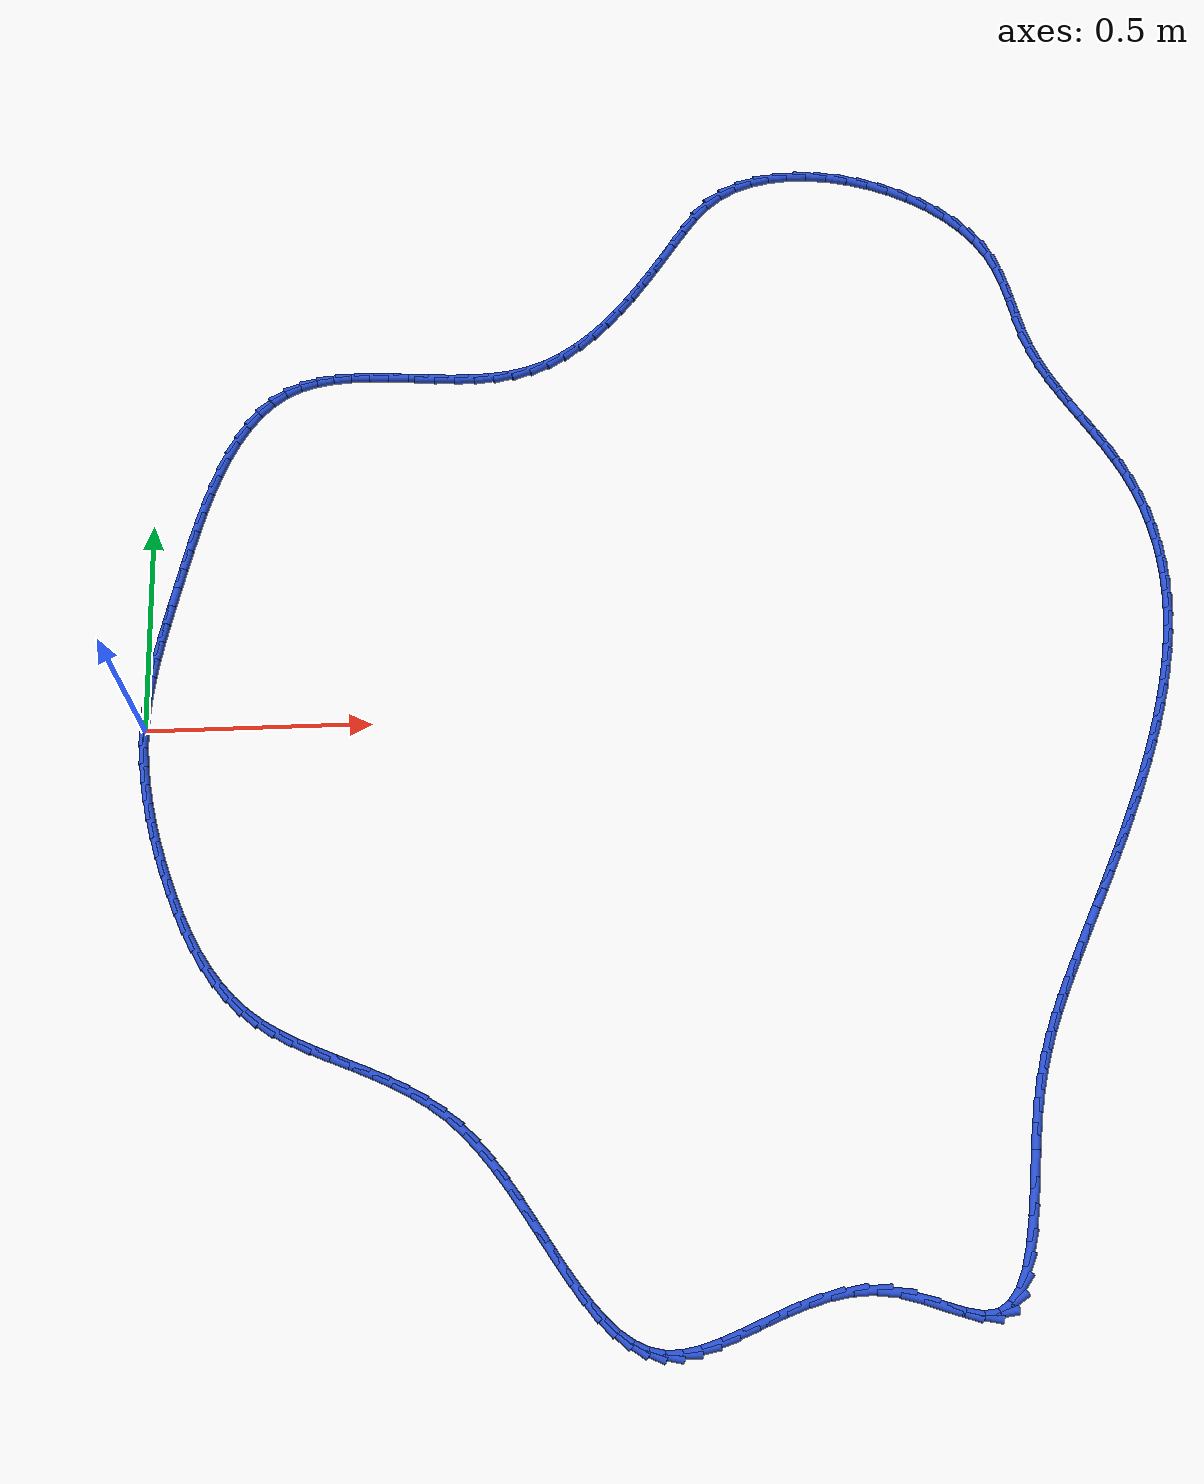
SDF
<sdf version="1.6">
 <world name="default">
  <light name="sun" type="directional">
   <pose>0 0 10 0 -0 0</pose>
   <diffuse>0.8 0.8 0.8 1</diffuse>
   <specular>0.2 0.2 0.2 1</specular>
   <attenuation>
    <range>1000</range>
    <constant>0.9</constant>
    <linear>0.01</linear>
    <quadratic>0.001</quadratic>
   </attenuation>
   <direction>-0.5 0.1 -0.9</direction>
  </light>
  <model name="ground_plane">
   <static>1</static>
   <link name="link">
    <collision name="collision">
     <geometry><plane><normal>0 0 1</normal><size>100 100</size></plane></geometry>
     <surface><friction><ode><mu>100</mu><mu2>50</mu2></ode></friction></surface>
    </collision>
    <visual name="visual">
     <cast_shadows>0</cast_shadows>
     <geometry><plane><normal>0 0 1</normal><size>100 100</size></plane></geometry>
     <material>
      <script><uri>file://media/materials/scripts/gazebo.material</uri><name>Gazebo/WhiteGlow</name></script>
     </material>
    </visual>
   </link>
  </model>
  <gravity>0 0 -9.8</gravity>
  <magnetic_field>6e-06 2.3e-05 -4.2e-05</magnetic_field>
  <atmosphere type="adiabatic"/>
  <physics name="default_physics" default="0" type="ode">
   <max_step_size>0.001</max_step_size>
   <real_time_factor>1</real_time_factor>
   <real_time_update_rate>1000</real_time_update_rate>
  </physics>
  <scene><ambient>0.4 0.4 0.4 1</ambient><background>0.7 0.7 0.7 1</background><shadows>1</shadows></scene>
  <spherical_coordinates>
   <surface_model>EARTH_WGS84</surface_model>
   <latitude_deg>0</latitude_deg>
   <longitude_deg>0</longitude_deg>
   <elevation>0</elevation>
   <heading_deg>0</heading_deg>
  </spherical_coordinates>
  <model name="line">
   <link name="link_0">
    <pose>5.204170427930421e-18 6.938893903907228e-18 0.01 0 1.57 1.525094738466744</pose>
    <collision name="collision">
     <geometry><cylinder><radius>0.01</radius><length>0.08</length></cylinder></geometry>
    </collision>
    <visual name="visual">
     <material>
      <script><name>Gazebo/Blue</name><uri>file://media/materials/scripts/gazebo.material</uri></script>
     </material>
     <geometry><cylinder><radius>0.01</radius><length>0.08</length></cylinder></geometry>
    </visual>
   </link>
   <link name="link_1">
    <pose>0.0019329707417370912 0.04226603205885977 0.01 0 1.57 1.4729227705149253</pose>
    <collision name="collision">
     <geometry><cylinder><radius>0.01</radius><length>0.08</length></cylinder></geometry>
    </collision>
    <visual name="visual">
     <material>
      <script><name>Gazebo/Blue</name><uri>file://media/materials/scripts/gazebo.material</uri></script>
     </material>
     <geometry><cylinder><radius>0.01</radius><length>0.08</length></cylinder></geometry>
    </visual>
   </link>
   <link name="link_2">
    <pose>0.006068385487758424 0.08438365567221005 0.01 0 1.57 1.428232375103234</pose>
    <collision name="collision">
     <geometry><cylinder><radius>0.01</radius><length>0.08</length></cylinder></geometry>
    </collision>
    <visual name="visual">
     <material>
      <script><name>Gazebo/Blue</name><uri>file://media/materials/scripts/gazebo.material</uri></script>
     </material>
     <geometry><cylinder><radius>0.01</radius><length>0.08</length></cylinder></geometry>
    </visual>
   </link>
   <link name="link_3">
    <pose>0.012123159333029498 0.1265661151327682 0.01 0 1.57 1.3916051796267443</pose>
    <collision name="collision">
     <geometry><cylinder><radius>0.01</radius><length>0.08</length></cylinder></geometry>
    </collision>
    <visual name="visual">
     <material>
      <script><name>Gazebo/Blue</name><uri>file://media/materials/scripts/gazebo.material</uri></script>
     </material>
     <geometry><cylinder><radius>0.01</radius><length>0.08</length></cylinder></geometry>
    </visual>
   </link>
   <link name="link_4">
    <pose>0.019814207372515828 0.1690266547332516 0.01 0 1.57 1.3632613175699397</pose>
    <collision name="collision">
     <geometry><cylinder><radius>0.01</radius><length>0.08</length></cylinder></geometry>
    </collision>
    <visual name="visual">
     <material>
      <script><name>Gazebo/Blue</name><uri>file://media/materials/scripts/gazebo.material</uri></script>
     </material>
     <geometry><cylinder><radius>0.01</radius><length>0.08</length></cylinder></geometry>
    </visual>
   </link>
   <link name="link_5">
    <pose>0.028858444701182907 0.2119785187663776 0.01 0 1.57 1.3431325112576995</pose>
    <collision name="collision">
     <geometry><cylinder><radius>0.01</radius><length>0.08</length></cylinder></geometry>
    </collision>
    <visual name="visual">
     <material>
      <script><name>Gazebo/Blue</name><uri>file://media/materials/scripts/gazebo.material</uri></script>
     </material>
     <geometry><cylinder><radius>0.01</radius><length>0.08</length></cylinder></geometry>
    </visual>
   </link>
   <link name="link_6">
    <pose>0.03897278641399622 0.25563495152486354 0.01 0 1.57 1.3309381764570511</pose>
    <collision name="collision">
     <geometry><cylinder><radius>0.01</radius><length>0.08</length></cylinder></geometry>
    </collision>
    <visual name="visual">
     <material>
      <script><name>Gazebo/Blue</name><uri>file://media/materials/scripts/gazebo.material</uri></script>
     </material>
     <geometry><cylinder><radius>0.01</radius><length>0.08</length></cylinder></geometry>
    </visual>
   </link>
   <link name="link_7">
    <pose>0.04987414760592131 0.30020919730142687 0.01 0 1.57 1.3262492758702555</pose>
    <collision name="collision">
     <geometry><cylinder><radius>0.01</radius><length>0.08</length></cylinder></geometry>
    </collision>
    <visual name="visual">
     <material>
      <script><name>Gazebo/Blue</name><uri>file://media/materials/scripts/gazebo.material</uri></script>
     </material>
     <geometry><cylinder><radius>0.01</radius><length>0.08</length></cylinder></geometry>
    </visual>
   </link>
   <link name="link_8">
    <pose>0.06127949614984447 0.3459144219004965 0.01 0 1.57 1.3254450662968764</pose>
    <collision name="collision">
     <geometry><cylinder><radius>0.01</radius><length>0.08</length></cylinder></geometry>
    </collision>
    <visual name="visual">
     <material>
      <script><name>Gazebo/Blue</name><uri>file://media/materials/scripts/gazebo.material</uri></script>
     </material>
     <geometry><cylinder><radius>0.01</radius><length>0.08</length></cylinder></geometry>
    </visual>
   </link>
   <link name="link_9">
    <pose>0.07301849977512503 0.3927961903815274 0.01 0 1.57 1.3187563874229709</pose>
    <collision name="collision">
     <geometry><cylinder><radius>0.01</radius><length>0.08</length></cylinder></geometry>
    </collision>
    <visual name="visual">
     <material>
      <script><name>Gazebo/Blue</name><uri>file://media/materials/scripts/gazebo.material</uri></script>
     </material>
     <geometry><cylinder><radius>0.01</radius><length>0.08</length></cylinder></geometry>
    </visual>
   </link>
   <link name="link_10">
    <pose>0.08527166106585296 0.440378326385168 0.01 0 1.57 1.3044386406866184</pose>
    <collision name="collision">
     <geometry><cylinder><radius>0.01</radius><length>0.08</length></cylinder></geometry>
    </collision>
    <visual name="visual">
     <material>
      <script><name>Gazebo/Blue</name><uri>file://media/materials/scripts/gazebo.material</uri></script>
     </material>
     <geometry><cylinder><radius>0.01</radius><length>0.08</length></cylinder></geometry>
    </visual>
   </link>
   <link name="link_11">
    <pose>0.09828755543242554 0.48808341955977375 0.01 0 1.57 1.2822154006803026</pose>
    <collision name="collision">
     <geometry><cylinder><radius>0.01</radius><length>0.08</length></cylinder></geometry>
    </collision>
    <visual name="visual">
     <material>
      <script><name>Gazebo/Blue</name><uri>file://media/materials/scripts/gazebo.material</uri></script>
     </material>
     <geometry><cylinder><radius>0.01</radius><length>0.08</length></cylinder></geometry>
    </visual>
   </link>
   <link name="link_12">
    <pose>0.11231475828524014 0.5353340595537002 0.01 0 1.57 1.2513681553846026</pose>
    <collision name="collision">
     <geometry><cylinder><radius>0.01</radius><length>0.08</length></cylinder></geometry>
    </collision>
    <visual name="visual">
     <material>
      <script><name>Gazebo/Blue</name><uri>file://media/materials/scripts/gazebo.material</uri></script>
     </material>
     <geometry><cylinder><radius>0.01</radius><length>0.08</length></cylinder></geometry>
    </visual>
   </link>
   <link name="link_13">
    <pose>0.12760184503469407 0.5815528360153028 0.01 0 1.57 1.2107098953116975</pose>
    <collision name="collision">
     <geometry><cylinder><radius>0.01</radius><length>0.08</length></cylinder></geometry>
    </collision>
    <visual name="visual">
     <material>
      <script><name>Gazebo/Blue</name><uri>file://media/materials/scripts/gazebo.material</uri></script>
     </material>
     <geometry><cylinder><radius>0.01</radius><length>0.08</length></cylinder></geometry>
    </visual>
   </link>
   <link name="link_14">
    <pose>0.14439739109118455 0.6261623385929374 0.01 0 1.57 1.1585323496470719</pose>
    <collision name="collision">
     <geometry><cylinder><radius>0.01</radius><length>0.08</length></cylinder></geometry>
    </collision>
    <visual name="visual">
     <material>
      <script><name>Gazebo/Blue</name><uri>file://media/materials/scripts/gazebo.material</uri></script>
     </material>
     <geometry><cylinder><radius>0.01</radius><length>0.08</length></cylinder></geometry>
    </visual>
   </link>
   <link name="link_15">
    <pose>0.162949971865109 0.6685851569349592 0.01 0 1.57 1.0925550231910814</pose>
    <collision name="collision">
     <geometry><cylinder><radius>0.01</radius><length>0.08</length></cylinder></geometry>
    </collision>
    <visual name="visual">
     <material>
      <script><name>Gazebo/Blue</name><uri>file://media/materials/scripts/gazebo.material</uri></script>
     </material>
     <geometry><cylinder><radius>0.01</radius><length>0.08</length></cylinder></geometry>
    </visual>
   </link>
   <link name="link_16">
    <pose>0.18350816276686466 0.708243880689724 0.01 0 1.57 1.0099406676055473</pose>
    <collision name="collision">
     <geometry><cylinder><radius>0.01</radius><length>0.08</length></cylinder></geometry>
    </collision>
    <visual name="visual">
     <material>
      <script><name>Gazebo/Blue</name><uri>file://media/materials/scripts/gazebo.material</uri></script>
     </material>
     <geometry><cylinder><radius>0.01</radius><length>0.08</length></cylinder></geometry>
    </visual>
   </link>
   <link name="link_17">
    <pose>0.20632053920684884 0.7445610995055869 0.01 0 1.57 0.9075173838801668</pose>
    <collision name="collision">
     <geometry><cylinder><radius>0.01</radius><length>0.08</length></cylinder></geometry>
    </collision>
    <visual name="visual">
     <material>
      <script><name>Gazebo/Blue</name><uri>file://media/materials/scripts/gazebo.material</uri></script>
     </material>
     <geometry><cylinder><radius>0.01</radius><length>0.08</length></cylinder></geometry>
    </visual>
   </link>
   <link name="link_18">
    <pose>0.23163567659545897 0.7769594030309042 0.01 0 1.57 0.7824590899361151</pose>
    <collision name="collision">
     <geometry><cylinder><radius>0.01</radius><length>0.08</length></cylinder></geometry>
    </collision>
    <visual name="visual">
     <material>
      <script><name>Gazebo/Blue</name><uri>file://media/materials/scripts/gazebo.material</uri></script>
     </material>
     <geometry><cylinder><radius>0.01</radius><length>0.08</length></cylinder></geometry>
    </visual>
   </link>
   <link name="link_19">
    <pose>0.25970215034309213 0.8048613809140304 0.01 0 1.57 0.6337157590089862</pose>
    <collision name="collision">
     <geometry><cylinder><radius>0.01</radius><length>0.08</length></cylinder></geometry>
    </collision>
    <visual name="visual">
     <material>
      <script><name>Gazebo/Blue</name><uri>file://media/materials/scripts/gazebo.material</uri></script>
     </material>
     <geometry><cylinder><radius>0.01</radius><length>0.08</length></cylinder></geometry>
    </visual>
   </link>
   <link name="link_20">
    <pose>0.29076853586014584 0.8276896228033219 0.01 0 1.57 0.46460197282267884</pose>
    <collision name="collision">
     <geometry><cylinder><radius>0.01</radius><length>0.08</length></cylinder></geometry>
    </collision>
    <visual name="visual">
     <material>
      <script><name>Gazebo/Blue</name><uri>file://media/materials/scripts/gazebo.material</uri></script>
     </material>
     <geometry><cylinder><radius>0.01</radius><length>0.08</length></cylinder></geometry>
    </visual>
   </link>
   <link name="link_21">
    <pose>0.3250751701278635 0.8448838857514581 0.01 0 1.57 0.30072754248889544</pose>
    <collision name="collision">
     <geometry><cylinder><radius>0.01</radius><length>0.08</length></cylinder></geometry>
    </collision>
    <visual name="visual">
     <material>
      <script><name>Gazebo/Blue</name><uri>file://media/materials/scripts/gazebo.material</uri></script>
     </material>
     <geometry><cylinder><radius>0.01</radius><length>0.08</length></cylinder></geometry>
    </visual>
   </link>
   <link name="link_22">
    <pose>0.3625620313049287 0.8565098205650031 0.01 0 1.57 0.17018543914863102</pose>
    <collision name="collision">
     <geometry><cylinder><radius>0.01</radius><length>0.08</length></cylinder></geometry>
    </collision>
    <visual name="visual">
     <material>
      <script><name>Gazebo/Blue</name><uri>file://media/materials/scripts/gazebo.material</uri></script>
     </material>
     <geometry><cylinder><radius>0.01</radius><length>0.08</length></cylinder></geometry>
    </visual>
   </link>
   <link name="link_23">
    <pose>0.4027900635809096 0.863422916656749 0.01 0 1.57 0.07294865082528965</pose>
    <collision name="collision">
     <geometry><cylinder><radius>0.01</radius><length>0.08</length></cylinder></geometry>
    </collision>
    <visual name="visual">
     <material>
      <script><name>Gazebo/Blue</name><uri>file://media/materials/scripts/gazebo.material</uri></script>
     </material>
     <geometry><cylinder><radius>0.01</radius><length>0.08</length></cylinder></geometry>
    </visual>
   </link>
   <link name="link_24">
    <pose>0.4452959702288152 0.8665291771488355 0.01 0 1.57 0.004635024791395739</pose>
    <collision name="collision">
     <geometry><cylinder><radius>0.01</radius><length>0.08</length></cylinder></geometry>
    </collision>
    <visual name="visual">
     <material>
      <script><name>Gazebo/Blue</name><uri>file://media/materials/scripts/gazebo.material</uri></script>
     </material>
     <geometry><cylinder><radius>0.01</radius><length>0.08</length></cylinder></geometry>
    </visual>
   </link>
   <link name="link_25">
    <pose>0.48961645452165553 0.8667346051634027 0.01 0 1.57 -0.03915956770169774</pose>
    <collision name="collision">
     <geometry><cylinder><radius>0.01</radius><length>0.08</length></cylinder></geometry>
    </collision>
    <visual name="visual">
     <material>
      <script><name>Gazebo/Blue</name><uri>file://media/materials/scripts/gazebo.material</uri></script>
     </material>
     <geometry><cylinder><radius>0.01</radius><length>0.08</length></cylinder></geometry>
    </visual>
   </link>
   <link name="link_26">
    <pose>0.5352882197324396 0.8649452038225897 0.01 0 1.57 -0.06173937045378747</pose>
    <collision name="collision">
     <geometry><cylinder><radius>0.01</radius><length>0.08</length></cylinder></geometry>
    </collision>
    <visual name="visual">
     <material>
      <script><name>Gazebo/Blue</name><uri>file://media/materials/scripts/gazebo.material</uri></script>
     </material>
     <geometry><cylinder><radius>0.01</radius><length>0.08</length></cylinder></geometry>
    </visual>
   </link>
   <link name="link_27">
    <pose>0.5818479691341764 0.8620669762485365 0.01 0 1.57 -0.06505836708120889</pose>
    <collision name="collision">
     <geometry><cylinder><radius>0.01</radius><length>0.08</length></cylinder></geometry>
    </collision>
    <visual name="visual">
     <material>
      <script><name>Gazebo/Blue</name><uri>file://media/materials/scripts/gazebo.material</uri></script>
     </material>
     <geometry><cylinder><radius>0.01</radius><length>0.08</length></cylinder></geometry>
    </visual>
   </link>
   <link name="link_28">
    <pose>0.6288324059998759 0.8590059255633825 0.01 0 1.57 -0.04975822230091679</pose>
    <collision name="collision">
     <geometry><cylinder><radius>0.01</radius><length>0.08</length></cylinder></geometry>
    </collision>
    <visual name="visual">
     <material>
      <script><name>Gazebo/Blue</name><uri>file://media/materials/scripts/gazebo.material</uri></script>
     </material>
     <geometry><cylinder><radius>0.01</radius><length>0.08</length></cylinder></geometry>
    </visual>
   </link>
   <link name="link_29">
    <pose>0.6757782336025469 0.8566680548892674 0.01 0 1.57 -0.01525781030413903</pose>
    <collision name="collision">
     <geometry><cylinder><radius>0.01</radius><length>0.08</length></cylinder></geometry>
    </collision>
    <visual name="visual">
     <material>
      <script><name>Gazebo/Blue</name><uri>file://media/materials/scripts/gazebo.material</uri></script>
     </material>
     <geometry><cylinder><radius>0.01</radius><length>0.08</length></cylinder></geometry>
    </visual>
   </link>
   <link name="link_30">
    <pose>0.7222221552151991 0.8559593673483314 0.01 0 1.57 0.040140041052352644</pose>
    <collision name="collision">
     <geometry><cylinder><radius>0.01</radius><length>0.08</length></cylinder></geometry>
    </collision>
    <visual name="visual">
     <material>
      <script><name>Gazebo/Blue</name><uri>file://media/materials/scripts/gazebo.material</uri></script>
     </material>
     <geometry><cylinder><radius>0.01</radius><length>0.08</length></cylinder></geometry>
    </visual>
   </link>
   <link name="link_31">
    <pose>0.7677008741108414 0.8577858660627132 0.01 0 1.57 0.11901851240756672</pose>
    <collision name="collision">
     <geometry><cylinder><radius>0.01</radius><length>0.08</length></cylinder></geometry>
    </collision>
    <visual name="visual">
     <material>
      <script><name>Gazebo/Blue</name><uri>file://media/materials/scripts/gazebo.material</uri></script>
     </material>
     <geometry><cylinder><radius>0.01</radius><length>0.08</length></cylinder></geometry>
    </visual>
   </link>
   <link name="link_32">
    <pose>0.8117510935624838 0.8630535541545534 0.01 0 1.57 0.2242295608768374</pose>
    <collision name="collision">
     <geometry><cylinder><radius>0.01</radius><length>0.08</length></cylinder></geometry>
    </collision>
    <visual name="visual">
     <material>
      <script><name>Gazebo/Blue</name><uri>file://media/materials/scripts/gazebo.material</uri></script>
     </material>
     <geometry><cylinder><radius>0.01</radius><length>0.08</length></cylinder></geometry>
    </visual>
   </link>
   <link name="link_33">
    <pose>0.8539095298272169 0.8726684059161346 0.01 0 1.57 0.35042733968477874</pose>
    <collision name="collision">
     <geometry><cylinder><radius>0.01</radius><length>0.08</length></cylinder></geometry>
    </collision>
    <visual name="visual">
     <material>
      <script><name>Gazebo/Blue</name><uri>file://media/materials/scripts/gazebo.material</uri></script>
     </material>
     <geometry><cylinder><radius>0.01</radius><length>0.08</length></cylinder></geometry>
    </visual>
   </link>
   <link name="link_34">
    <pose>0.8938363939251674 0.8872621878568051 0.01 0 1.57 0.47140945866218326</pose>
    <collision name="collision">
     <geometry><cylinder><radius>0.01</radius><length>0.08</length></cylinder></geometry>
    </collision>
    <visual name="visual">
     <material>
      <script><name>Gazebo/Blue</name><uri>file://media/materials/scripts/gazebo.material</uri></script>
     </material>
     <geometry><cylinder><radius>0.01</radius><length>0.08</length></cylinder></geometry>
    </visual>
   </link>
   <link name="link_35">
    <pose>0.9316178357801687 0.9065209117058699 0.01 0 1.57 0.5788615417983258</pose>
    <collision name="collision">
     <geometry><cylinder><radius>0.01</radius><length>0.08</length></cylinder></geometry>
    </collision>
    <visual name="visual">
     <material>
      <script><name>Gazebo/Blue</name><uri>file://media/materials/scripts/gazebo.material</uri></script>
     </material>
     <geometry><cylinder><radius>0.01</radius><length>0.08</length></cylinder></geometry>
    </visual>
   </link>
   <link name="link_36">
    <pose>0.9674317679813005 0.9299268393624787 0.01 0 1.57 0.671433389481857</pose>
    <collision name="collision">
     <geometry><cylinder><radius>0.01</radius><length>0.08</length></cylinder></geometry>
    </collision>
    <visual name="visual">
     <material>
      <script><name>Gazebo/Blue</name><uri>file://media/materials/scripts/gazebo.material</uri></script>
     </material>
     <geometry><cylinder><radius>0.01</radius><length>0.08</length></cylinder></geometry>
    </visual>
   </link>
   <link name="link_37">
    <pose>1.0014561031176432 0.9569622327257811 0.01 0 1.57 0.7492001396432475</pose>
    <collision name="collision">
     <geometry><cylinder><radius>0.01</radius><length>0.08</length></cylinder></geometry>
    </collision>
    <visual name="visual">
     <material>
      <script><name>Gazebo/Blue</name><uri>file://media/materials/scripts/gazebo.material</uri></script>
     </material>
     <geometry><cylinder><radius>0.01</radius><length>0.08</length></cylinder></geometry>
    </visual>
   </link>
   <link name="link_38">
    <pose>1.0338687537782765 0.9871093536949266 0.01 0 1.57 0.8130469851833928</pose>
    <collision name="collision">
     <geometry><cylinder><radius>0.01</radius><length>0.08</length></cylinder></geometry>
    </collision>
    <visual name="visual">
     <material>
      <script><name>Gazebo/Blue</name><uri>file://media/materials/scripts/gazebo.material</uri></script>
     </material>
     <geometry><cylinder><radius>0.01</radius><length>0.08</length></cylinder></geometry>
    </visual>
   </link>
   <link name="link_39">
    <pose>1.0648476325522809 1.019850464169065 0.01 0 1.57 0.8641674827874622</pose>
    <collision name="collision">
     <geometry><cylinder><radius>0.01</radius><length>0.08</length></cylinder></geometry>
    </collision>
    <visual name="visual">
     <material>
      <script><name>Gazebo/Blue</name><uri>file://media/materials/scripts/gazebo.material</uri></script>
     </material>
     <geometry><cylinder><radius>0.01</radius><length>0.08</length></cylinder></geometry>
    </visual>
   </link>
   <link name="link_40">
    <pose>1.0945706520287357 1.0546678260473454 0.01 0 1.57 0.9037397082736272</pose>
    <collision name="collision">
     <geometry><cylinder><radius>0.01</radius><length>0.08</length></cylinder></geometry>
    </collision>
    <visual name="visual">
     <material>
      <script><name>Gazebo/Blue</name><uri>file://media/materials/scripts/gazebo.material</uri></script>
     </material>
     <geometry><cylinder><radius>0.01</radius><length>0.08</length></cylinder></geometry>
    </visual>
   </link>
   <link name="link_41">
    <pose>1.1232157247967214 1.0910437012289176 0.01 0 1.57 0.9327472343714757</pose>
    <collision name="collision">
     <geometry><cylinder><radius>0.01</radius><length>0.08</length></cylinder></geometry>
    </collision>
    <visual name="visual">
     <material>
      <script><name>Gazebo/Blue</name><uri>file://media/materials/scripts/gazebo.material</uri></script>
     </material>
     <geometry><cylinder><radius>0.01</radius><length>0.08</length></cylinder></geometry>
    </visual>
   </link>
   <link name="link_42">
    <pose>1.1509607634453185 1.1284603516129317 0.01 0 1.57 0.9518895597640141</pose>
    <collision name="collision">
     <geometry><cylinder><radius>0.01</radius><length>0.08</length></cylinder></geometry>
    </collision>
    <visual name="visual">
     <material>
      <script><name>Gazebo/Blue</name><uri>file://media/materials/scripts/gazebo.material</uri></script>
     </material>
     <geometry><cylinder><radius>0.01</radius><length>0.08</length></cylinder></geometry>
    </visual>
   </link>
   <link name="link_43">
    <pose>1.1779836805636061 1.1664000390985363 0.01 0 1.57 0.9615360526253954</pose>
    <collision name="collision">
     <geometry><cylinder><radius>0.01</radius><length>0.08</length></cylinder></geometry>
    </collision>
    <visual name="visual">
     <material>
      <script><name>Gazebo/Blue</name><uri>file://media/materials/scripts/gazebo.material</uri></script>
     </material>
     <geometry><cylinder><radius>0.01</radius><length>0.08</length></cylinder></geometry>
    </visual>
   </link>
   <link name="link_44">
    <pose>1.204462388740665 1.2043450255848815 0.01 0 1.57 0.9593256630030895</pose>
    <collision name="collision">
     <geometry><cylinder><radius>0.01</radius><length>0.08</length></cylinder></geometry>
    </collision>
    <visual name="visual">
     <material>
      <script><name>Gazebo/Blue</name><uri>file://media/materials/scripts/gazebo.material</uri></script>
     </material>
     <geometry><cylinder><radius>0.01</radius><length>0.08</length></cylinder></geometry>
    </visual>
   </link>
   <link name="link_45">
    <pose>1.2306582837165776 1.2417084752740883 0.01 0 1.57 0.9216330524843448</pose>
    <collision name="collision">
     <geometry><cylinder><radius>0.01</radius><length>0.08</length></cylinder></geometry>
    </collision>
    <visual name="visual">
     <material>
      <script><name>Gazebo/Blue</name><uri>file://media/materials/scripts/gazebo.material</uri></script>
     </material>
     <geometry><cylinder><radius>0.01</radius><length>0.08</length></cylinder></geometry>
    </visual>
   </link>
   <link name="link_46">
    <pose>1.2576271893634026 1.2772460166414241 0.01 0 1.57 0.8320853243066894</pose>
    <collision name="collision">
     <geometry><cylinder><radius>0.01</radius><length>0.08</length></cylinder></geometry>
    </collision>
    <visual name="visual">
     <material>
      <script><name>Gazebo/Blue</name><uri>file://media/materials/scripts/gazebo.material</uri></script>
     </material>
     <geometry><cylinder><radius>0.01</radius><length>0.08</length></cylinder></geometry>
    </visual>
   </link>
   <link name="link_47">
    <pose>1.286864618445405 1.3093493545500774 0.01 0 1.57 0.6868609556460089</pose>
    <collision name="collision">
     <geometry><cylinder><radius>0.01</radius><length>0.08</length></cylinder></geometry>
    </collision>
    <visual name="visual">
     <material>
      <script><name>Gazebo/Blue</name><uri>file://media/materials/scripts/gazebo.material</uri></script>
     </material>
     <geometry><cylinder><radius>0.01</radius><length>0.08</length></cylinder></geometry>
    </visual>
   </link>
   <link name="link_48">
    <pose>1.3198644207140238 1.3364115824981786 0.01 0 1.57 0.5103191789274998</pose>
    <collision name="collision">
     <geometry><cylinder><radius>0.01</radius><length>0.08</length></cylinder></geometry>
    </collision>
    <visual name="visual">
     <material>
      <script><name>Gazebo/Blue</name><uri>file://media/materials/scripts/gazebo.material</uri></script>
     </material>
     <geometry><cylinder><radius>0.01</radius><length>0.08</length></cylinder></geometry>
    </visual>
   </link>
   <link name="link_49">
    <pose>1.3574002284757194 1.3574232956948902 0.01 0 1.57 0.34904825450279187</pose>
    <collision name="collision">
     <geometry><cylinder><radius>0.01</radius><length>0.08</length></cylinder></geometry>
    </collision>
    <visual name="visual">
     <material>
      <script><name>Gazebo/Blue</name><uri>file://media/materials/scripts/gazebo.material</uri></script>
     </material>
     <geometry><cylinder><radius>0.01</radius><length>0.08</length></cylinder></geometry>
    </visual>
   </link>
   <link name="link_50">
    <pose>1.3988701127188239 1.3725162728168745 0.01 0 1.57 0.20824848502652107</pose>
    <collision name="collision">
     <geometry><cylinder><radius>0.01</radius><length>0.08</length></cylinder></geometry>
    </collision>
    <visual name="visual">
     <material>
      <script><name>Gazebo/Blue</name><uri>file://media/materials/scripts/gazebo.material</uri></script>
     </material>
     <geometry><cylinder><radius>0.01</radius><length>0.08</length></cylinder></geometry>
    </visual>
   </link>
   <link name="link_51">
    <pose>1.4435172927375701 1.3819507595098002 0.01 0 1.57 0.08554469255284418</pose>
    <collision name="collision">
     <geometry><cylinder><radius>0.01</radius><length>0.08</length></cylinder></geometry>
    </collision>
    <visual name="visual">
     <material>
      <script><name>Gazebo/Blue</name><uri>file://media/materials/scripts/gazebo.material</uri></script>
     </material>
     <geometry><cylinder><radius>0.01</radius><length>0.08</length></cylinder></geometry>
    </visual>
   </link>
   <link name="link_52">
    <pose>1.4905849878261894 1.3859870014193345 0.01 0 1.57 -0.022604909702360565</pose>
    <collision name="collision">
     <geometry><cylinder><radius>0.01</radius><length>0.08</length></cylinder></geometry>
    </collision>
    <visual name="visual">
     <material>
      <script><name>Gazebo/Blue</name><uri>file://media/materials/scripts/gazebo.material</uri></script>
     </material>
     <geometry><cylinder><radius>0.01</radius><length>0.08</length></cylinder></geometry>
    </visual>
   </link>
   <link name="link_53">
    <pose>1.5393164172789136 1.3848852441911461 0.01 0 1.57 -0.11988378303092485</pose>
    <collision name="collision">
     <geometry><cylinder><radius>0.01</radius><length>0.08</length></cylinder></geometry>
    </collision>
    <visual name="visual">
     <material>
      <script><name>Gazebo/Blue</name><uri>file://media/materials/scripts/gazebo.material</uri></script>
     </material>
     <geometry><cylinder><radius>0.01</radius><length>0.08</length></cylinder></geometry>
    </visual>
   </link>
   <link name="link_54">
    <pose>1.5889548003899734 1.3789057334709018 0.01 0 1.57 -0.20971110903520798</pose>
    <collision name="collision">
     <geometry><cylinder><radius>0.01</radius><length>0.08</length></cylinder></geometry>
    </collision>
    <visual name="visual">
     <material>
      <script><name>Gazebo/Blue</name><uri>file://media/materials/scripts/gazebo.material</uri></script>
     </material>
     <geometry><cylinder><radius>0.01</radius><length>0.08</length></cylinder></geometry>
    </visual>
   </link>
   <link name="link_55">
    <pose>1.6387433564536023 1.368308714904271 0.01 0 1.57 -0.2951777173246071</pose>
    <collision name="collision">
     <geometry><cylinder><radius>0.01</radius><length>0.08</length></cylinder></geometry>
    </collision>
    <visual name="visual">
     <material>
      <script><name>Gazebo/Blue</name><uri>file://media/materials/scripts/gazebo.material</uri></script>
     </material>
     <geometry><cylinder><radius>0.01</radius><length>0.08</length></cylinder></geometry>
    </visual>
   </link>
   <link name="link_56">
    <pose>1.6879253047640304 1.353354434136921 0.01 0 1.57 -0.37913321990971155</pose>
    <collision name="collision">
     <geometry><cylinder><radius>0.01</radius><length>0.08</length></cylinder></geometry>
    </collision>
    <visual name="visual">
     <material>
      <script><name>Gazebo/Blue</name><uri>file://media/materials/scripts/gazebo.material</uri></script>
     </material>
     <geometry><cylinder><radius>0.01</radius><length>0.08</length></cylinder></geometry>
    </visual>
   </link>
   <link name="link_57">
    <pose>1.7357438646154904 1.33430313681452 0.01 0 1.57 -0.464327889590246</pose>
    <collision name="collision">
     <geometry><cylinder><radius>0.01</radius><length>0.08</length></cylinder></geometry>
    </collision>
    <visual name="visual">
     <material>
      <script><name>Gazebo/Blue</name><uri>file://media/materials/scripts/gazebo.material</uri></script>
     </material>
     <geometry><cylinder><radius>0.01</radius><length>0.08</length></cylinder></geometry>
    </visual>
   </link>
   <link name="link_58">
    <pose>1.7814422553022136 1.311415068582735 0.01 0 1.57 -0.5535657005975273</pose>
    <collision name="collision">
     <geometry><cylinder><radius>0.01</radius><length>0.08</length></cylinder></geometry>
    </collision>
    <visual name="visual">
     <material>
      <script><name>Gazebo/Blue</name><uri>file://media/materials/scripts/gazebo.material</uri></script>
     </material>
     <geometry><cylinder><radius>0.01</radius><length>0.08</length></cylinder></geometry>
    </visual>
   </link>
   <link name="link_59">
    <pose>1.824263696118432 1.2849504750872356 0.01 0 1.57 -0.6498415488152488</pose>
    <collision name="collision">
     <geometry><cylinder><radius>0.01</radius><length>0.08</length></cylinder></geometry>
    </collision>
    <visual name="visual">
     <material>
      <script><name>Gazebo/Blue</name><uri>file://media/materials/scripts/gazebo.material</uri></script>
     </material>
     <geometry><cylinder><radius>0.01</radius><length>0.08</length></cylinder></geometry>
    </visual>
   </link>
   <link name="link_60">
    <pose>1.8634514063583778 1.2551696019736889 0.01 0 1.57 -0.7564224979733709</pose>
    <collision name="collision">
     <geometry><cylinder><radius>0.01</radius><length>0.08</length></cylinder></geometry>
    </collision>
    <visual name="visual">
     <material>
      <script><name>Gazebo/Blue</name><uri>file://media/materials/scripts/gazebo.material</uri></script>
     </material>
     <geometry><cylinder><radius>0.01</radius><length>0.08</length></cylinder></geometry>
    </visual>
   </link>
   <link name="link_61">
    <pose>1.8982486053162817 1.2223326948877635 0.01 0 1.57 -0.8767873375099471</pose>
    <collision name="collision">
     <geometry><cylinder><radius>0.01</radius><length>0.08</length></cylinder></geometry>
    </collision>
    <visual name="visual">
     <material>
      <script><name>Gazebo/Blue</name><uri>file://media/materials/scripts/gazebo.material</uri></script>
     </material>
     <geometry><cylinder><radius>0.01</radius><length>0.08</length></cylinder></geometry>
    </visual>
   </link>
   <link name="link_62">
    <pose>1.9278985122863759 1.1866999994751266 0.01 0 1.57 -1.0140951849079383</pose>
    <collision name="collision">
     <geometry><cylinder><radius>0.01</radius><length>0.08</length></cylinder></geometry>
    </collision>
    <visual name="visual">
     <material>
      <script><name>Gazebo/Blue</name><uri>file://media/materials/scripts/gazebo.material</uri></script>
     </material>
     <geometry><cylinder><radius>0.01</radius><length>0.08</length></cylinder></geometry>
    </visual>
   </link>
   <link name="link_63">
    <pose>1.9516522587270428 1.148533000109518 0.01 0 1.57 -1.152823407134523</pose>
    <collision name="collision">
     <geometry><cylinder><radius>0.01</radius><length>0.08</length></cylinder></geometry>
    </collision>
    <visual name="visual">
     <material>
      <script><name>Gazebo/Blue</name><uri>file://media/materials/scripts/gazebo.material</uri></script>
     </material>
     <geometry><cylinder><radius>0.01</radius><length>0.08</length></cylinder></geometry>
    </visual>
   </link>
   <link name="link_64">
    <pose>1.969557921998301 1.1082179509799934 0.01 0 1.57 -1.2571346984092242</pose>
    <collision name="collision">
     <geometry><cylinder><radius>0.01</radius><length>0.08</length></cylinder></geometry>
    </collision>
    <visual name="visual">
     <material>
      <script><name>Gazebo/Blue</name><uri>file://media/materials/scripts/gazebo.material</uri></script>
     </material>
     <geometry><cylinder><radius>0.01</radius><length>0.08</length></cylinder></geometry>
    </visual>
   </link>
   <link name="link_65">
    <pose>1.9831318101678033 1.0663709724106336 0.01 0 1.57 -1.3207150122558236</pose>
    <collision name="collision">
     <geometry><cylinder><radius>0.01</radius><length>0.08</length></cylinder></geometry>
    </collision>
    <visual name="visual">
     <material>
      <script><name>Gazebo/Blue</name><uri>file://media/materials/scripts/gazebo.material</uri></script>
     </material>
     <geometry><cylinder><radius>0.01</radius><length>0.08</length></cylinder></geometry>
    </visual>
   </link>
   <link name="link_66">
    <pose>1.9940483244339688 1.0236329357791185 0.01 0 1.57 -1.3437063531771798</pose>
    <collision name="collision">
     <geometry><cylinder><radius>0.01</radius><length>0.08</length></cylinder></geometry>
    </collision>
    <visual name="visual">
     <material>
      <script><name>Gazebo/Blue</name><uri>file://media/materials/scripts/gazebo.material</uri></script>
     </material>
     <geometry><cylinder><radius>0.01</radius><length>0.08</length></cylinder></geometry>
    </visual>
   </link>
   <link name="link_67">
    <pose>2.0039818659952173 0.9806447124631309 0.01 0 1.57 -1.3263571677263284</pose>
    <collision name="collision">
     <geometry><cylinder><radius>0.01</radius><length>0.08</length></cylinder></geometry>
    </collision>
    <visual name="visual">
     <material>
      <script><name>Gazebo/Blue</name><uri>file://media/materials/scripts/gazebo.material</uri></script>
     </material>
     <geometry><cylinder><radius>0.01</radius><length>0.08</length></cylinder></geometry>
    </visual>
   </link>
   <link name="link_68">
    <pose>2.014606836049967 0.9380471738403512 0.01 0 1.57 -1.2679081254345785</pose>
    <collision name="collision">
     <geometry><cylinder><radius>0.01</radius><length>0.08</length></cylinder></geometry>
    </collision>
    <visual name="visual">
     <material>
      <script><name>Gazebo/Blue</name><uri>file://media/materials/scripts/gazebo.material</uri></script>
     </material>
     <geometry><cylinder><radius>0.01</radius><length>0.08</length></cylinder></geometry>
    </visual>
   </link>
   <link name="link_69">
    <pose>2.0275964998101252 0.89648073643125 0.01 0 1.57 -1.1821190737814526</pose>
    <collision name="collision">
     <geometry><cylinder><radius>0.01</radius><length>0.08</length></cylinder></geometry>
    </collision>
    <visual name="visual">
     <material>
      <script><name>Gazebo/Blue</name><uri>file://media/materials/scripts/gazebo.material</uri></script>
     </material>
     <geometry><cylinder><radius>0.01</radius><length>0.08</length></cylinder></geometry>
    </visual>
   </link>
   <link name="link_70">
    <pose>2.044031088809471 0.8563483617851805 0.01 0 1.57 -1.1084543636718092</pose>
    <collision name="collision">
     <geometry><cylinder><radius>0.01</radius><length>0.08</length></cylinder></geometry>
    </collision>
    <visual name="visual">
     <material>
      <script><name>Gazebo/Blue</name><uri>file://media/materials/scripts/gazebo.material</uri></script>
     </material>
     <geometry><cylinder><radius>0.01</radius><length>0.08</length></cylinder></geometry>
    </visual>
   </link>
   <link name="link_71">
    <pose>2.0634281408960753 0.8174272976047241 0.01 0 1.57 -1.0538577785639751</pose>
    <collision name="collision">
     <geometry><cylinder><radius>0.01</radius><length>0.08</length></cylinder></geometry>
    </collision>
    <visual name="visual">
     <material>
      <script><name>Gazebo/Blue</name><uri>file://media/materials/scripts/gazebo.material</uri></script>
     </material>
     <geometry><cylinder><radius>0.01</radius><length>0.08</length></cylinder></geometry>
    </visual>
   </link>
   <link name="link_72">
    <pose>2.085050820488224 0.779392938632588 0.01 0 1.57 -1.0181427933414056</pose>
    <collision name="collision">
     <geometry><cylinder><radius>0.01</radius><length>0.08</length></cylinder></geometry>
    </collision>
    <visual name="visual">
     <material>
      <script><name>Gazebo/Blue</name><uri>file://media/materials/scripts/gazebo.material</uri></script>
     </material>
     <geometry><cylinder><radius>0.01</radius><length>0.08</length></cylinder></geometry>
    </visual>
   </link>
   <link name="link_73">
    <pose>2.1081622920042045 0.7419206796114794 0.01 0 1.57 -1.000851249320041</pose>
    <collision name="collision">
     <geometry><cylinder><radius>0.01</radius><length>0.08</length></cylinder></geometry>
    </collision>
    <visual name="visual">
     <material>
      <script><name>Gazebo/Blue</name><uri>file://media/materials/scripts/gazebo.material</uri></script>
     </material>
     <geometry><cylinder><radius>0.01</radius><length>0.08</length></cylinder></geometry>
    </visual>
   </link>
   <link name="link_74">
    <pose>2.132025719862304 0.704685915284105 0.01 0 1.57 -1.0016247844464188</pose>
    <collision name="collision">
     <geometry><cylinder><radius>0.01</radius><length>0.08</length></cylinder></geometry>
    </collision>
    <visual name="visual">
     <material>
      <script><name>Gazebo/Blue</name><uri>file://media/materials/scripts/gazebo.material</uri></script>
     </material>
     <geometry><cylinder><radius>0.01</radius><length>0.08</length></cylinder></geometry>
    </visual>
   </link>
   <link name="link_75">
    <pose>2.155904268480809 0.6673640403931729 0.01 0 1.57 -1.020369365184333</pose>
    <collision name="collision">
     <geometry><cylinder><radius>0.01</radius><length>0.08</length></cylinder></geometry>
    </collision>
    <visual name="visual">
     <material>
      <script><name>Gazebo/Blue</name><uri>file://media/materials/scripts/gazebo.material</uri></script>
     </material>
     <geometry><cylinder><radius>0.01</radius><length>0.08</length></cylinder></geometry>
    </visual>
   </link>
   <link name="link_76">
    <pose>2.1790611022780064 0.6296304496813893 0.01 0 1.57 -1.057243417890719</pose>
    <collision name="collision">
     <geometry><cylinder><radius>0.01</radius><length>0.08</length></cylinder></geometry>
    </collision>
    <visual name="visual">
     <material>
      <script><name>Gazebo/Blue</name><uri>file://media/materials/scripts/gazebo.material</uri></script>
     </material>
     <geometry><cylinder><radius>0.01</radius><length>0.08</length></cylinder></geometry>
    </visual>
   </link>
   <link name="link_77">
    <pose>2.200759385672183 0.5911605378914613 0.01 0 1.57 -1.1124662582189528</pose>
    <collision name="collision">
     <geometry><cylinder><radius>0.01</radius><length>0.08</length></cylinder></geometry>
    </collision>
    <visual name="visual">
     <material>
      <script><name>Gazebo/Blue</name><uri>file://media/materials/scripts/gazebo.material</uri></script>
     </material>
     <geometry><cylinder><radius>0.01</radius><length>0.08</length></cylinder></geometry>
    </visual>
   </link>
   <link name="link_78">
    <pose>2.220262598159185 0.5516299882652347 0.01 0 1.57 -1.180949639768087</pose>
    <collision name="collision">
     <geometry><cylinder><radius>0.01</radius><length>0.08</length></cylinder></geometry>
    </collision>
    <visual name="visual">
     <material>
      <script><name>Gazebo/Blue</name><uri>file://media/materials/scripts/gazebo.material</uri></script>
     </material>
     <geometry><cylinder><radius>0.01</radius><length>0.08</length></cylinder></geometry>
    </visual>
   </link>
   <link name="link_79">
    <pose>2.237008294876006 0.5108738755055513 0.01 0 1.57 -1.2494610498458565</pose>
    <collision name="collision">
     <geometry><cylinder><radius>0.01</radius><length>0.08</length></cylinder></geometry>
    </collision>
    <visual name="visual">
     <material>
      <script><name>Gazebo/Blue</name><uri>file://media/materials/scripts/gazebo.material</uri></script>
     </material>
     <geometry><cylinder><radius>0.01</radius><length>0.08</length></cylinder></geometry>
    </visual>
   </link>
   <link name="link_80">
    <pose>2.250896699474961 0.46915091434970824 0.01 0 1.57 -1.3165749980136106</pose>
    <collision name="collision">
     <geometry><cylinder><radius>0.01</radius><length>0.08</length></cylinder></geometry>
    </collision>
    <visual name="visual">
     <material>
      <script><name>Gazebo/Blue</name><uri>file://media/materials/scripts/gazebo.material</uri></script>
     </material>
     <geometry><cylinder><radius>0.01</radius><length>0.08</length></cylinder></geometry>
    </visual>
   </link>
   <link name="link_81">
    <pose>2.2619040534130606 0.4267894160465061 0.01 0 1.57 -1.382648691737762</pose>
    <collision name="collision">
     <geometry><cylinder><radius>0.01</radius><length>0.08</length></cylinder></geometry>
    </collision>
    <visual name="visual">
     <material>
      <script><name>Gazebo/Blue</name><uri>file://media/materials/scripts/gazebo.material</uri></script>
     </material>
     <geometry><cylinder><radius>0.01</radius><length>0.08</length></cylinder></geometry>
    </visual>
   </link>
   <link name="link_82">
    <pose>2.2700392349920593 0.38406254152364466 0.01 0 1.57 -1.446249874943885</pose>
    <collision name="collision">
     <geometry><cylinder><radius>0.01</radius><length>0.08</length></cylinder></geometry>
    </collision>
    <visual name="visual">
     <material>
      <script><name>Gazebo/Blue</name><uri>file://media/materials/scripts/gazebo.material</uri></script>
     </material>
     <geometry><cylinder><radius>0.01</radius><length>0.08</length></cylinder></geometry>
    </visual>
   </link>
   <link name="link_83">
    <pose>2.275423781124191 0.34105307918382954 0.01 0 1.57 -1.506613651423778</pose>
    <collision name="collision">
     <geometry><cylinder><radius>0.01</radius><length>0.08</length></cylinder></geometry>
    </collision>
    <visual name="visual">
     <material>
      <script><name>Gazebo/Blue</name><uri>file://media/materials/scripts/gazebo.material</uri></script>
     </material>
     <geometry><cylinder><radius>0.01</radius><length>0.08</length></cylinder></geometry>
    </visual>
   </link>
   <link name="link_84">
    <pose>2.278203519685037 0.29780277012758266 0.01 0 1.57 -1.5634141090888278</pose>
    <collision name="collision">
     <geometry><cylinder><radius>0.01</radius><length>0.08</length></cylinder></geometry>
    </collision>
    <visual name="visual">
     <material>
      <script><name>Gazebo/Blue</name><uri>file://media/materials/scripts/gazebo.material</uri></script>
     </material>
     <geometry><cylinder><radius>0.01</radius><length>0.08</length></cylinder></geometry>
    </visual>
   </link>
   <link name="link_85">
    <pose>2.278524278550183 0.2543533554554244 0.01 0 1.57 1.5251380988046166</pose>
    <collision name="collision">
     <geometry><cylinder><radius>0.01</radius><length>0.08</length></cylinder></geometry>
    </collision>
    <visual name="visual">
     <material>
      <script><name>Gazebo/Blue</name><uri>file://media/materials/scripts/gazebo.material</uri></script>
     </material>
     <geometry><cylinder><radius>0.01</radius><length>0.08</length></cylinder></geometry>
    </visual>
   </link>
   <link name="link_86">
    <pose>2.27653188559521 0.21074657626787652 0.01 0 1.57 1.4759425711324763</pose>
    <collision name="collision">
     <geometry><cylinder><radius>0.01</radius><length>0.08</length></cylinder></geometry>
    </collision>
    <visual name="visual">
     <material>
      <script><name>Gazebo/Blue</name><uri>file://media/materials/scripts/gazebo.material</uri></script>
     </material>
     <geometry><cylinder><radius>0.01</radius><length>0.08</length></cylinder></geometry>
    </visual>
   </link>
   <link name="link_87">
    <pose>2.272372168695703 0.16702417366546002 0.01 0 1.57 1.4305868336575038</pose>
    <collision name="collision">
     <geometry><cylinder><radius>0.01</radius><length>0.08</length></cylinder></geometry>
    </collision>
    <visual name="visual">
     <material>
      <script><name>Gazebo/Blue</name><uri>file://media/materials/scripts/gazebo.material</uri></script>
     </material>
     <geometry><cylinder><radius>0.01</radius><length>0.08</length></cylinder></geometry>
    </visual>
   </link>
   <link name="link_88">
    <pose>2.266190955727243 0.12322788874869521 0.01 0 1.57 1.388998250799786</pose>
    <collision name="collision">
     <geometry><cylinder><radius>0.01</radius><length>0.08</length></cylinder></geometry>
    </collision>
    <visual name="visual">
     <material>
      <script><name>Gazebo/Blue</name><uri>file://media/materials/scripts/gazebo.material</uri></script>
     </material>
     <geometry><cylinder><radius>0.01</radius><length>0.08</length></cylinder></geometry>
    </visual>
   </link>
   <link name="link_89">
    <pose>2.2581340745654166 0.07939946261810443 0.01 0 1.57 1.3510575698864697</pose>
    <collision name="collision">
     <geometry><cylinder><radius>0.01</radius><length>0.08</length></cylinder></geometry>
    </collision>
    <visual name="visual">
     <material>
      <script><name>Gazebo/Blue</name><uri>file://media/materials/scripts/gazebo.material</uri></script>
     </material>
     <geometry><cylinder><radius>0.01</radius><length>0.08</length></cylinder></geometry>
    </visual>
   </link>
   <link name="link_90">
    <pose>2.2483473530858054 0.035580636374208274 0.01 0 1.57 1.316616870848242</pose>
    <collision name="collision">
     <geometry><cylinder><radius>0.01</radius><length>0.08</length></cylinder></geometry>
    </collision>
    <visual name="visual">
     <material>
      <script><name>Gazebo/Blue</name><uri>file://media/materials/scripts/gazebo.material</uri></script>
     </material>
     <geometry><cylinder><radius>0.01</radius><length>0.08</length></cylinder></geometry>
    </visual>
   </link>
   <link name="link_91">
    <pose>2.236976619163992 -0.008186848882472089 0.01 0 1.57 1.2855141276721478</pose>
    <collision name="collision">
     <geometry><cylinder><radius>0.01</radius><length>0.08</length></cylinder></geometry>
    </collision>
    <visual name="visual">
     <material>
      <script><name>Gazebo/Blue</name><uri>file://media/materials/scripts/gazebo.material</uri></script>
     </material>
     <geometry><cylinder><radius>0.01</radius><length>0.08</length></cylinder></geometry>
    </visual>
   </link>
   <link name="link_92">
    <pose>2.224167700675561 -0.0518612520514165 0.01 0 1.57 1.2575844973854422</pose>
    <collision name="collision">
     <geometry><cylinder><radius>0.01</radius><length>0.08</length></cylinder></geometry>
    </collision>
    <visual name="visual">
     <material>
      <script><name>Gazebo/Blue</name><uri>file://media/materials/scripts/gazebo.material</uri></script>
     </material>
     <geometry><cylinder><radius>0.01</radius><length>0.08</length></cylinder></geometry>
    </visual>
   </link>
   <link name="link_93">
    <pose>2.210066425496096 -0.095400832032102 0.01 0 1.57 1.2326687595561678</pose>
    <collision name="collision">
     <geometry><cylinder><radius>0.01</radius><length>0.08</length></cylinder></geometry>
    </collision>
    <visual name="visual">
     <material>
      <script><name>Gazebo/Blue</name><uri>file://media/materials/scripts/gazebo.material</uri></script>
     </material>
     <geometry><cylinder><radius>0.01</radius><length>0.08</length></cylinder></geometry>
    </visual>
   </link>
   <link name="link_94">
    <pose>2.1948186215011796 -0.13876384772400832 0.01 0 1.57 1.2106194526416034</pose>
    <collision name="collision">
     <geometry><cylinder><radius>0.01</radius><length>0.08</length></cylinder></geometry>
    </collision>
    <visual name="visual">
     <material>
      <script><name>Gazebo/Blue</name><uri>file://media/materials/scripts/gazebo.material</uri></script>
     </material>
     <geometry><cylinder><radius>0.01</radius><length>0.08</length></cylinder></geometry>
    </visual>
   </link>
   <link name="link_95">
    <pose>2.1785701165663953 -0.18190855802661443 0.01 0 1.57 1.191305263471172</pose>
    <collision name="collision">
     <geometry><cylinder><radius>0.01</radius><length>0.08</length></cylinder></geometry>
    </collision>
    <visual name="visual">
     <material>
      <script><name>Gazebo/Blue</name><uri>file://media/materials/scripts/gazebo.material</uri></script>
     </material>
     <geometry><cylinder><radius>0.01</radius><length>0.08</length></cylinder></geometry>
    </visual>
   </link>
   <link name="link_96">
    <pose>2.1614667385673263 -0.22479322183939898 0.01 0 1.57 1.1746141773821444</pose>
    <collision name="collision">
     <geometry><cylinder><radius>0.01</radius><length>0.08</length></cylinder></geometry>
    </collision>
    <visual name="visual">
     <material>
      <script><name>Gazebo/Blue</name><uri>file://media/materials/scripts/gazebo.material</uri></script>
     </material>
     <geometry><cylinder><radius>0.01</radius><length>0.08</length></cylinder></geometry>
    </visual>
   </link>
   <link name="link_97">
    <pose>2.143654315379557 -0.2673760980618411 0.01 0 1.57 1.1604558256636974</pose>
    <collision name="collision">
     <geometry><cylinder><radius>0.01</radius><length>0.08</length></cylinder></geometry>
    </collision>
    <visual name="visual">
     <material>
      <script><name>Gazebo/Blue</name><uri>file://media/materials/scripts/gazebo.material</uri></script>
     </material>
     <geometry><cylinder><radius>0.01</radius><length>0.08</length></cylinder></geometry>
    </visual>
   </link>
   <link name="link_98">
    <pose>2.1252786748786683 -0.30961544559342036 0.01 0 1.57 1.1487633957455161</pose>
    <collision name="collision">
     <geometry><cylinder><radius>0.01</radius><length>0.08</length></cylinder></geometry>
    </collision>
    <visual name="visual">
     <material>
      <script><name>Gazebo/Blue</name><uri>file://media/materials/scripts/gazebo.material</uri></script>
     </material>
     <geometry><cylinder><radius>0.01</radius><length>0.08</length></cylinder></geometry>
    </visual>
   </link>
   <link name="link_99">
    <pose>2.1064856449402463 -0.35146952333361386 0.01 0 1.57 1.1394954093336753</pose>
    <collision name="collision">
     <geometry><cylinder><radius>0.01</radius><length>0.08</length></cylinder></geometry>
    </collision>
    <visual name="visual">
     <material>
      <script><name>Gazebo/Blue</name><uri>file://media/materials/scripts/gazebo.material</uri></script>
     </material>
     <geometry><cylinder><radius>0.01</radius><length>0.08</length></cylinder></geometry>
    </visual>
   </link>
   <link name="link_100">
    <pose>2.0874210534398734 -0.39289659018190154 0.01 0 1.57 1.1326376293907519</pose>
    <collision name="collision">
     <geometry><cylinder><radius>0.01</radius><length>0.08</length></cylinder></geometry>
    </collision>
    <visual name="visual">
     <material>
      <script><name>Gazebo/Blue</name><uri>file://media/materials/scripts/gazebo.material</uri></script>
     </material>
     <geometry><cylinder><radius>0.01</radius><length>0.08</length></cylinder></geometry>
    </visual>
   </link>
   <link name="link_101">
    <pose>2.0682307282531327 -0.4338549050377619 0.01 0 1.57 1.1282053298941332</pose>
    <collision name="collision">
     <geometry><cylinder><radius>0.01</radius><length>0.08</length></cylinder></geometry>
    </collision>
    <visual name="visual">
     <material>
      <script><name>Gazebo/Blue</name><uri>file://media/materials/scripts/gazebo.material</uri></script>
     </material>
     <geometry><cylinder><radius>0.01</radius><length>0.08</length></cylinder></geometry>
    </visual>
   </link>
   <link name="link_102">
    <pose>2.0490604972556077 -0.4743027268006743 0.01 0 1.57 1.1262461524184804</pose>
    <collision name="collision">
     <geometry><cylinder><radius>0.01</radius><length>0.08</length></cylinder></geometry>
    </collision>
    <visual name="visual">
     <material>
      <script><name>Gazebo/Blue</name><uri>file://media/materials/scripts/gazebo.material</uri></script>
     </material>
     <geometry><cylinder><radius>0.01</radius><length>0.08</length></cylinder></geometry>
    </visual>
   </link>
   <link name="link_103">
    <pose>2.0300561883228814 -0.5141983143701181 0.01 0 1.57 1.1268437797459807</pose>
    <collision name="collision">
     <geometry><cylinder><radius>0.01</radius><length>0.08</length></cylinder></geometry>
    </collision>
    <visual name="visual">
     <material>
      <script><name>Gazebo/Blue</name><uri>file://media/materials/scripts/gazebo.material</uri></script>
     </material>
     <geometry><cylinder><radius>0.01</radius><length>0.08</length></cylinder></geometry>
    </visual>
   </link>
   <link name="link_104">
    <pose>2.0113636293305377 -0.5534999266455706 0.01 0 1.57 1.1301226773317021</pose>
    <collision name="collision">
     <geometry><cylinder><radius>0.01</radius><length>0.08</length></cylinder></geometry>
    </collision>
    <visual name="visual">
     <material>
      <script><name>Gazebo/Blue</name><uri>file://media/materials/scripts/gazebo.material</uri></script>
     </material>
     <geometry><cylinder><radius>0.01</radius><length>0.08</length></cylinder></geometry>
    </visual>
   </link>
   <link name="link_105">
    <pose>1.9931286481541601 -0.5921658225265114 0.01 0 1.57 1.1367173516193283</pose>
    <collision name="collision">
     <geometry><cylinder><radius>0.01</radius><length>0.08</length></cylinder></geometry>
    </collision>
    <visual name="visual">
     <material>
      <script><name>Gazebo/Blue</name><uri>file://media/materials/scripts/gazebo.material</uri></script>
     </material>
     <geometry><cylinder><radius>0.01</radius><length>0.08</length></cylinder></geometry>
    </visual>
   </link>
   <link name="link_106">
    <pose>1.975497254566834 -0.6301999904116558 0.01 0 1.57 1.1508856920942594</pose>
    <collision name="collision">
     <geometry><cylinder><radius>0.01</radius><length>0.08</length></cylinder></geometry>
    </collision>
    <visual name="visual">
     <material>
      <script><name>Gazebo/Blue</name><uri>file://media/materials/scripts/gazebo.material</uri></script>
     </material>
     <geometry><cylinder><radius>0.01</radius><length>0.08</length></cylinder></geometry>
    </visual>
   </link>
   <link name="link_107">
    <pose>1.9586170577549775 -0.6680085153173835 0.01 0 1.57 1.174559866336844</pose>
    <collision name="collision">
     <geometry><cylinder><radius>0.01</radius><length>0.08</length></cylinder></geometry>
    </collision>
    <visual name="visual">
     <material>
      <script><name>Gazebo/Blue</name><uri>file://media/materials/scripts/gazebo.material</uri></script>
     </material>
     <geometry><cylinder><radius>0.01</radius><length>0.08</length></cylinder></geometry>
    </visual>
   </link>
   <link name="link_108">
    <pose>1.9426364973639414 -0.7062062617686775 0.01 0 1.57 1.2068670798294112</pose>
    <collision name="collision">
     <geometry><cylinder><radius>0.01</radius><length>0.08</length></cylinder></geometry>
    </collision>
    <visual name="visual">
     <material>
      <script><name>Gazebo/Blue</name><uri>file://media/materials/scripts/gazebo.material</uri></script>
     </material>
     <geometry><cylinder><radius>0.01</radius><length>0.08</length></cylinder></geometry>
    </visual>
   </link>
   <link name="link_109">
    <pose>1.9277040201119364 -0.7454098724250724 0.01 0 1.57 1.2462433965528794</pose>
    <collision name="collision">
     <geometry><cylinder><radius>0.01</radius><length>0.08</length></cylinder></geometry>
    </collision>
    <visual name="visual">
     <material>
      <script><name>Gazebo/Blue</name><uri>file://media/materials/scripts/gazebo.material</uri></script>
     </material>
     <geometry><cylinder><radius>0.01</radius><length>0.08</length></cylinder></geometry>
    </visual>
   </link>
   <link name="link_110">
    <pose>1.9139680727171726 -0.7862359899460993 0.01 0 1.57 1.2906383329548197</pose>
    <collision name="collision">
     <geometry><cylinder><radius>0.01</radius><length>0.08</length></cylinder></geometry>
    </collision>
    <visual name="visual">
     <material>
      <script><name>Gazebo/Blue</name><uri>file://media/materials/scripts/gazebo.material</uri></script>
     </material>
     <geometry><cylinder><radius>0.01</radius><length>0.08</length></cylinder></geometry>
    </visual>
   </link>
   <link name="link_111">
    <pose>1.9015771018978596 -0.8293012569912924 0.01 0 1.57 1.3377959567780278</pose>
    <collision name="collision">
     <geometry><cylinder><radius>0.01</radius><length>0.08</length></cylinder></geometry>
    </collision>
    <visual name="visual">
     <material>
      <script><name>Gazebo/Blue</name><uri>file://media/materials/scripts/gazebo.material</uri></script>
     </material>
     <geometry><cylinder><radius>0.01</radius><length>0.08</length></cylinder></geometry>
    </visual>
   </link>
   <link name="link_112">
    <pose>1.890679554372208 -0.875222316220185 0.01 0 1.57 1.3855578351796385</pose>
    <collision name="collision">
     <geometry><cylinder><radius>0.01</radius><length>0.08</length></cylinder></geometry>
    </collision>
    <visual name="visual">
     <material>
      <script><name>Gazebo/Blue</name><uri>file://media/materials/scripts/gazebo.material</uri></script>
     </material>
     <geometry><cylinder><radius>0.01</radius><length>0.08</length></cylinder></geometry>
    </visual>
   </link>
   <link name="link_113">
    <pose>1.881423872641485 -0.9246158000600668 0.01 0 1.57 1.4274538944313124</pose>
    <collision name="collision">
     <geometry><cylinder><radius>0.01</radius><length>0.08</length></cylinder></geometry>
    </collision>
    <visual name="visual">
     <material>
      <script><name>Gazebo/Blue</name><uri>file://media/materials/scripts/gazebo.material</uri></script>
     </material>
     <geometry><cylinder><radius>0.01</radius><length>0.08</length></cylinder></geometry>
    </visual>
   </link>
   <link name="link_114">
    <pose>1.8737704656949628 -0.977642085148311 0.01 0 1.57 1.4484611724034604</pose>
    <collision name="collision">
     <geometry><cylinder><radius>0.01</radius><length>0.08</length></cylinder></geometry>
    </collision>
    <visual name="visual">
     <material>
      <script><name>Gazebo/Blue</name><uri>file://media/materials/scripts/gazebo.material</uri></script>
     </material>
     <geometry><cylinder><radius>0.01</radius><length>0.08</length></cylinder></geometry>
    </visual>
   </link>
   <link name="link_115">
    <pose>1.8669902577652049 -1.0327885409600348 0.01 0 1.57 1.4487047729486515</pose>
    <collision name="collision">
     <geometry><cylinder><radius>0.01</radius><length>0.08</length></cylinder></geometry>
    </collision>
    <visual name="visual">
     <material>
      <script><name>Gazebo/Blue</name><uri>file://media/materials/scripts/gazebo.material</uri></script>
     </material>
     <geometry><cylinder><radius>0.01</radius><length>0.08</length></cylinder></geometry>
    </visual>
   </link>
   <link name="link_116">
    <pose>1.860196179506628 -1.0881591718774257 0.01 0 1.57 1.4284656932392459</pose>
    <collision name="collision">
     <geometry><cylinder><radius>0.01</radius><length>0.08</length></cylinder></geometry>
    </collision>
    <visual name="visual">
     <material>
      <script><name>Gazebo/Blue</name><uri>file://media/materials/scripts/gazebo.material</uri></script>
     </material>
     <geometry><cylinder><radius>0.01</radius><length>0.08</length></cylinder></geometry>
    </visual>
   </link>
   <link name="link_117">
    <pose>1.8525011615736482 -1.141857982282674 0.01 0 1.57 1.3838404599639171</pose>
    <collision name="collision">
     <geometry><cylinder><radius>0.01</radius><length>0.08</length></cylinder></geometry>
    </collision>
    <visual name="visual">
     <material>
      <script><name>Gazebo/Blue</name><uri>file://media/materials/scripts/gazebo.material</uri></script>
     </material>
     <geometry><cylinder><radius>0.01</radius><length>0.08</length></cylinder></geometry>
    </visual>
   </link>
   <link name="link_118">
    <pose>1.8430181346206813 -1.1919889765579685 0.01 0 1.57 1.305041402375887</pose>
    <collision name="collision">
     <geometry><cylinder><radius>0.01</radius><length>0.08</length></cylinder></geometry>
    </collision>
    <visual name="visual">
     <material>
      <script><name>Gazebo/Blue</name><uri>file://media/materials/scripts/gazebo.material</uri></script>
     </material>
     <geometry><cylinder><radius>0.01</radius><length>0.08</length></cylinder></geometry>
    </visual>
   </link>
   <link name="link_119">
    <pose>1.8308600293021446 -1.2366561590854996 0.01 0 1.57 1.172003325556206</pose>
    <collision name="collision">
     <geometry><cylinder><radius>0.01</radius><length>0.08</length></cylinder></geometry>
    </collision>
    <visual name="visual">
     <material>
      <script><name>Gazebo/Blue</name><uri>file://media/materials/scripts/gazebo.material</uri></script>
     </material>
     <geometry><cylinder><radius>0.01</radius><length>0.08</length></cylinder></geometry>
    </visual>
   </link>
   <link name="link_120">
    <pose>1.8151397762724546 -1.2739635342474576 0.01 0 1.57 0.9474230164833984</pose>
    <collision name="collision">
     <geometry><cylinder><radius>0.01</radius><length>0.08</length></cylinder></geometry>
    </collision>
    <visual name="visual">
     <material>
      <script><name>Gazebo/Blue</name><uri>file://media/materials/scripts/gazebo.material</uri></script>
     </material>
     <geometry><cylinder><radius>0.01</radius><length>0.08</length></cylinder></geometry>
    </visual>
   </link>
   <link name="link_121">
    <pose>1.794970306186028 -1.3020151064260295 0.01 0 1.57 0.5851726504949478</pose>
    <collision name="collision">
     <geometry><cylinder><radius>0.01</radius><length>0.08</length></cylinder></geometry>
    </collision>
    <visual name="visual">
     <material>
      <script><name>Gazebo/Blue</name><uri>file://media/materials/scripts/gazebo.material</uri></script>
     </material>
     <geometry><cylinder><radius>0.01</radius><length>0.08</length></cylinder></geometry>
    </visual>
   </link>
   <link name="link_122">
    <pose>1.7694645496972814 -1.318914880003406 0.01 0 1.57 0.12445242362076123</pose>
    <collision name="collision">
     <geometry><cylinder><radius>0.01</radius><length>0.08</length></cylinder></geometry>
    </collision>
    <visual name="visual">
     <material>
      <script><name>Gazebo/Blue</name><uri>file://media/materials/scripts/gazebo.material</uri></script>
     </material>
     <geometry><cylinder><radius>0.01</radius><length>0.08</length></cylinder></geometry>
    </visual>
   </link>
   <link name="link_123">
    <pose>1.7377739859226728 -1.3228793363391889 0.01 0 1.57 -0.200181198032541</pose>
    <collision name="collision">
     <geometry><cylinder><radius>0.01</radius><length>0.08</length></cylinder></geometry>
    </collision>
    <visual name="visual">
     <material>
      <script><name>Gazebo/Blue</name><uri>file://media/materials/scripts/gazebo.material</uri></script>
     </material>
     <geometry><cylinder><radius>0.01</radius><length>0.08</length></cylinder></geometry>
    </visual>
   </link>
   <link name="link_124">
    <pose>1.7001172948835093 -1.3152388432027422 0.01 0 1.57 -0.33028567664919845</pose>
    <collision name="collision">
     <geometry><cylinder><radius>0.01</radius><length>0.08</length></cylinder></geometry>
    </collision>
    <visual name="visual">
     <material>
      <script><name>Gazebo/Blue</name><uri>file://media/materials/scripts/gazebo.material</uri></script>
     </material>
     <geometry><cylinder><radius>0.01</radius><length>0.08</length></cylinder></geometry>
    </visual>
   </link>
   <link name="link_125">
    <pose>1.6578915123358329 -1.3007619831284174 0.01 0 1.57 -0.34644932131385475</pose>
    <collision name="collision">
     <geometry><cylinder><radius>0.01</radius><length>0.08</length></cylinder></geometry>
    </collision>
    <visual name="visual">
     <material>
      <script><name>Gazebo/Blue</name><uri>file://media/materials/scripts/gazebo.material</uri></script>
     </material>
     <geometry><cylinder><radius>0.01</radius><length>0.08</length></cylinder></geometry>
    </visual>
   </link>
   <link name="link_126">
    <pose>1.6125545219003377 -1.284394880983916 0.01 0 1.57 -0.27604376772454353</pose>
    <collision name="collision">
     <geometry><cylinder><radius>0.01</radius><length>0.08</length></cylinder></geometry>
    </collision>
    <visual name="visual">
     <material>
      <script><name>Gazebo/Blue</name><uri>file://media/materials/scripts/gazebo.material</uri></script>
     </material>
     <geometry><cylinder><radius>0.01</radius><length>0.08</length></cylinder></geometry>
    </visual>
   </link>
   <link name="link_127">
    <pose>1.5655642071977183 -1.2710836616369405 0.01 0 1.57 -0.12078740658803738</pose>
    <collision name="collision">
     <geometry><cylinder><radius>0.01</radius><length>0.08</length></cylinder></geometry>
    </collision>
    <visual name="visual">
     <material>
      <script><name>Gazebo/Blue</name><uri>file://media/materials/scripts/gazebo.material</uri></script>
     </material>
     <geometry><cylinder><radius>0.01</radius><length>0.08</length></cylinder></geometry>
    </visual>
   </link>
   <link name="link_128">
    <pose>1.518296709242475 -1.265346414592049 0.01 0 1.57 0.05029705700655284</pose>
    <collision name="collision">
     <geometry><cylinder><radius>0.01</radius><length>0.08</length></cylinder></geometry>
    </collision>
    <visual name="visual">
     <material>
      <script><name>Gazebo/Blue</name><uri>file://media/materials/scripts/gazebo.material</uri></script>
     </material>
     <geometry><cylinder><radius>0.01</radius><length>0.08</length></cylinder></geometry>
    </visual>
   </link>
   <link name="link_129">
    <pose>1.4713657467661545 -1.267708896420571 0.01 0 1.57 0.1877252016706743</pose>
    <collision name="collision">
     <geometry><cylinder><radius>0.01</radius><length>0.08</length></cylinder></geometry>
    </collision>
    <visual name="visual">
     <material>
      <script><name>Gazebo/Blue</name><uri>file://media/materials/scripts/gazebo.material</uri></script>
     </material>
     <geometry><cylinder><radius>0.01</radius><length>0.08</length></cylinder></geometry>
    </visual>
   </link>
   <link name="link_130">
    <pose>1.4249697710529101 -1.2765223654618352 0.01 0 1.57 0.2893231796785826</pose>
    <collision name="collision">
     <geometry><cylinder><radius>0.01</radius><length>0.08</length></cylinder></geometry>
    </collision>
    <visual name="visual">
     <material>
      <script><name>Gazebo/Blue</name><uri>file://media/materials/scripts/gazebo.material</uri></script>
     </material>
     <geometry><cylinder><radius>0.01</radius><length>0.08</length></cylinder></geometry>
    </visual>
   </link>
   <link name="link_131">
    <pose>1.3793030628193415 -1.2901162413778782 0.01 0 1.57 0.35730062820029046</pose>
    <collision name="collision">
     <geometry><cylinder><radius>0.01</radius><length>0.08</length></cylinder></geometry>
    </collision>
    <visual name="visual">
     <material>
      <script><name>Gazebo/Blue</name><uri>file://media/materials/scripts/gazebo.material</uri></script>
     </material>
     <geometry><cylinder><radius>0.01</radius><length>0.08</length></cylinder></geometry>
    </visual>
   </link>
   <link name="link_132">
    <pose>1.3345599027820498 -1.3068199438307366 0.01 0 1.57 0.3941215345359071</pose>
    <collision name="collision">
     <geometry><cylinder><radius>0.01</radius><length>0.08</length></cylinder></geometry>
    </collision>
    <visual name="visual">
     <material>
      <script><name>Gazebo/Blue</name><uri>file://media/materials/scripts/gazebo.material</uri></script>
     </material>
     <geometry><cylinder><radius>0.01</radius><length>0.08</length></cylinder></geometry>
    </visual>
   </link>
   <link name="link_133">
    <pose>1.2909345716576335 -1.3249628924824466 0.01 0 1.57 0.4004384264701907</pose>
    <collision name="collision">
     <geometry><cylinder><radius>0.01</radius><length>0.08</length></cylinder></geometry>
    </collision>
    <visual name="visual">
     <material>
      <script><name>Gazebo/Blue</name><uri>file://media/materials/scripts/gazebo.material</uri></script>
     </material>
     <geometry><cylinder><radius>0.01</radius><length>0.08</length></cylinder></geometry>
    </visual>
   </link>
   <link name="link_134">
    <pose>1.248621350162693 -1.3428745069950458 0.01 0 1.57 0.3738759360738634</pose>
    <collision name="collision">
     <geometry><cylinder><radius>0.01</radius><length>0.08</length></cylinder></geometry>
    </collision>
    <visual name="visual">
     <material>
      <script><name>Gazebo/Blue</name><uri>file://media/materials/scripts/gazebo.material</uri></script>
     </material>
     <geometry><cylinder><radius>0.01</radius><length>0.08</length></cylinder></geometry>
    </visual>
   </link>
   <link name="link_135">
    <pose>1.207814519013828 -1.3588842070305707 0.01 0 1.57 0.3079212565531423</pose>
    <collision name="collision">
     <geometry><cylinder><radius>0.01</radius><length>0.08</length></cylinder></geometry>
    </collision>
    <visual name="visual">
     <material>
      <script><name>Gazebo/Blue</name><uri>file://media/materials/scripts/gazebo.material</uri></script>
     </material>
     <geometry><cylinder><radius>0.01</radius><length>0.08</length></cylinder></geometry>
    </visual>
   </link>
   <link name="link_136">
    <pose>1.1687083589276375 -1.371321412251057 0.01 0 1.57 0.1909762075728887</pose>
    <collision name="collision">
     <geometry><cylinder><radius>0.01</radius><length>0.08</length></cylinder></geometry>
    </collision>
    <visual name="visual">
     <material>
      <script><name>Gazebo/Blue</name><uri>file://media/materials/scripts/gazebo.material</uri></script>
     </material>
     <geometry><cylinder><radius>0.01</radius><length>0.08</length></cylinder></geometry>
    </visual>
   </link>
   <link name="link_137">
    <pose>1.131497150620721 -1.3785155423185427 0.01 0 1.57 0.00800130340259082</pose>
    <collision name="collision">
     <geometry><cylinder><radius>0.01</radius><length>0.08</length></cylinder></geometry>
    </collision>
    <visual name="visual">
     <material>
      <script><name>Gazebo/Blue</name><uri>file://media/materials/scripts/gazebo.material</uri></script>
     </material>
     <geometry><cylinder><radius>0.01</radius><length>0.08</length></cylinder></geometry>
    </visual>
   </link>
   <link name="link_138">
    <pose>1.0963750646653139 -1.378796570781657 0.01 0 1.57 -0.23026580055183332</pose>
    <collision name="collision">
     <geometry><cylinder><radius>0.01</radius><length>0.08</length></cylinder></geometry>
    </collision>
    <visual name="visual">
     <material>
      <script><name>Gazebo/Blue</name><uri>file://media/materials/scripts/gazebo.material</uri></script>
     </material>
     <geometry><cylinder><radius>0.01</radius><length>0.08</length></cylinder></geometry>
    </visual>
   </link>
   <link name="link_139">
    <pose>1.0634215293695404 -1.3710714793836298 0.01 0 1.57 -0.45424558994043807</pose>
    <collision name="collision">
     <geometry><cylinder><radius>0.01</radius><length>0.08</length></cylinder></geometry>
    </collision>
    <visual name="visual">
     <material>
      <script><name>Gazebo/Blue</name><uri>file://media/materials/scripts/gazebo.material</uri></script>
     </material>
     <geometry><cylinder><radius>0.01</radius><length>0.08</length></cylinder></geometry>
    </visual>
   </link>
   <link name="link_140">
    <pose>1.0323841569179895 -1.355915864513487 0.01 0 1.57 -0.6355337480167395</pose>
    <collision name="collision">
     <geometry><cylinder><radius>0.01</radius><length>0.08</length></cylinder></geometry>
    </collision>
    <visual name="visual">
     <material>
      <script><name>Gazebo/Blue</name><uri>file://media/materials/scripts/gazebo.material</uri></script>
     </material>
     <geometry><cylinder><radius>0.01</radius><length>0.08</length></cylinder></geometry>
    </visual>
   </link>
   <link name="link_141">
    <pose>1.0029509288916563 -1.3342051889363356 0.01 0 1.57 -0.7718781894130441</pose>
    <collision name="collision">
     <geometry><cylinder><radius>0.01</radius><length>0.08</length></cylinder></geometry>
    </collision>
    <visual name="visual">
     <material>
      <script><name>Gazebo/Blue</name><uri>file://media/materials/scripts/gazebo.material</uri></script>
     </material>
     <geometry><cylinder><radius>0.01</radius><length>0.08</length></cylinder></geometry>
    </visual>
   </link>
   <link name="link_142">
    <pose>0.9748098268715358 -1.306814915417285 0.01 0 1.57 -0.8699970417854505</pose>
    <collision name="collision">
     <geometry><cylinder><radius>0.01</radius><length>0.08</length></cylinder></geometry>
    </collision>
    <visual name="visual">
     <material>
      <script><name>Gazebo/Blue</name><uri>file://media/materials/scripts/gazebo.material</uri></script>
     </material>
     <geometry><cylinder><radius>0.01</radius><length>0.08</length></cylinder></geometry>
    </visual>
   </link>
   <link name="link_143">
    <pose>0.9476488324386247 -1.274620506721444 0.01 0 1.57 -0.937999863923272</pose>
    <collision name="collision">
     <geometry><cylinder><radius>0.01</radius><length>0.08</length></cylinder></geometry>
    </collision>
    <visual name="visual">
     <material>
      <script><name>Gazebo/Blue</name><uri>file://media/materials/scripts/gazebo.material</uri></script>
     </material>
     <geometry><cylinder><radius>0.01</radius><length>0.08</length></cylinder></geometry>
    </visual>
   </link>
   <link name="link_144">
    <pose>0.9211559271739183 -1.238497425613922 0.01 0 1.57 -0.9824526091765833</pose>
    <collision name="collision">
     <geometry><cylinder><radius>0.01</radius><length>0.08</length></cylinder></geometry>
    </collision>
    <visual name="visual">
     <material>
      <script><name>Gazebo/Blue</name><uri>file://media/materials/scripts/gazebo.material</uri></script>
     </material>
     <geometry><cylinder><radius>0.01</radius><length>0.08</length></cylinder></geometry>
    </visual>
   </link>
   <link name="link_145">
    <pose>0.8950190926584121 -1.1993211348598278 0.01 0 1.57 -1.0079219767999836</pose>
    <collision name="collision">
     <geometry><cylinder><radius>0.01</radius><length>0.08</length></cylinder></geometry>
    </collision>
    <visual name="visual">
     <material>
      <script><name>Gazebo/Blue</name><uri>file://media/materials/scripts/gazebo.material</uri></script>
     </material>
     <geometry><cylinder><radius>0.01</radius><length>0.08</length></cylinder></geometry>
    </visual>
   </link>
   <link name="link_146">
    <pose>0.8689263104731018 -1.15796709722427 0.01 0 1.57 -1.017261127790327</pose>
    <collision name="collision">
     <geometry><cylinder><radius>0.01</radius><length>0.08</length></cylinder></geometry>
    </collision>
    <visual name="visual">
     <material>
      <script><name>Gazebo/Blue</name><uri>file://media/materials/scripts/gazebo.material</uri></script>
     </material>
     <geometry><cylinder><radius>0.01</radius><length>0.08</length></cylinder></geometry>
    </visual>
   </link>
   <link name="link_147">
    <pose>0.8425655621989827 -1.1153107754723572 0.01 0 1.57 -1.0119672369317636</pose>
    <collision name="collision">
     <geometry><cylinder><radius>0.01</radius><length>0.08</length></cylinder></geometry>
    </collision>
    <visual name="visual">
     <material>
      <script><name>Gazebo/Blue</name><uri>file://media/materials/scripts/gazebo.material</uri></script>
     </material>
     <geometry><cylinder><radius>0.01</radius><length>0.08</length></cylinder></geometry>
    </visual>
   </link>
   <link name="link_148">
    <pose>0.8156248294170502 -1.0722276323691977 0.01 0 1.57 -0.9924399138090572</pose>
    <collision name="collision">
     <geometry><cylinder><radius>0.01</radius><length>0.08</length></cylinder></geometry>
    </collision>
    <visual name="visual">
     <material>
      <script><name>Gazebo/Blue</name><uri>file://media/materials/scripts/gazebo.material</uri></script>
     </material>
     <geometry><cylinder><radius>0.01</radius><length>0.08</length></cylinder></geometry>
    </visual>
   </link>
   <link name="link_149">
    <pose>0.7877920937083005 -1.029593130679902 0.01 0 1.57 -0.9581319108410102</pose>
    <collision name="collision">
     <geometry><cylinder><radius>0.01</radius><length>0.08</length></cylinder></geometry>
    </collision>
    <visual name="visual">
     <material>
      <script><name>Gazebo/Blue</name><uri>file://media/materials/scripts/gazebo.material</uri></script>
     </material>
     <geometry><cylinder><radius>0.01</radius><length>0.08</length></cylinder></geometry>
    </visual>
   </link>
   <link name="link_150">
    <pose>0.7587553366537296 -0.9882827331695783 0.01 0 1.57 -0.9076336572436129</pose>
    <collision name="collision">
     <geometry><cylinder><radius>0.01</radius><length>0.08</length></cylinder></geometry>
    </collision>
    <visual name="visual">
     <material>
      <script><name>Gazebo/Blue</name><uri>file://media/materials/scripts/gazebo.material</uri></script>
     </material>
     <geometry><cylinder><radius>0.01</radius><length>0.08</length></cylinder></geometry>
    </visual>
   </link>
   <link name="link_151">
    <pose>0.728202539834332 -0.9491719026033347 0.01 0 1.57 -0.8387693023964465</pose>
    <collision name="collision">
     <geometry><cylinder><radius>0.01</radius><length>0.08</length></cylinder></geometry>
    </collision>
    <visual name="visual">
     <material>
      <script><name>Gazebo/Blue</name><uri>file://media/materials/scripts/gazebo.material</uri></script>
     </material>
     <geometry><cylinder><radius>0.01</radius><length>0.08</length></cylinder></geometry>
    </visual>
   </link>
   <link name="link_152">
    <pose>0.6958216848311041 -0.913136101746281 0.01 0 1.57 -0.7491656632248654</pose>
    <collision name="collision">
     <geometry><cylinder><radius>0.01</radius><length>0.08</length></cylinder></geometry>
    </collision>
    <visual name="visual">
     <material>
      <script><name>Gazebo/Blue</name><uri>file://media/materials/scripts/gazebo.material</uri></script>
     </material>
     <geometry><cylinder><radius>0.01</radius><length>0.08</length></cylinder></geometry>
    </visual>
   </link>
   <link name="link_153">
    <pose>0.6613075633830103 -0.8810366146142539 0.01 0 1.57 -0.6513825485336865</pose>
    <collision name="collision">
     <geometry><cylinder><radius>0.01</radius><length>0.08</length></cylinder></geometry>
    </collision>
    <visual name="visual">
     <material>
      <script><name>Gazebo/Blue</name><uri>file://media/materials/scripts/gazebo.material</uri></script>
     </material>
     <geometry><cylinder><radius>0.01</radius><length>0.08</length></cylinder></geometry>
    </visual>
   </link>
   <link name="link_154">
    <pose>0.6246609504639482 -0.8530976681109361 0.01 0 1.57 -0.5672356165106364</pose>
    <collision name="collision">
     <geometry><cylinder><radius>0.01</radius><length>0.08</length></cylinder></geometry>
    </collision>
    <visual name="visual">
     <material>
      <script><name>Gazebo/Blue</name><uri>file://media/materials/scripts/gazebo.material</uri></script>
     </material>
     <geometry><cylinder><radius>0.01</radius><length>0.08</length></cylinder></geometry>
    </visual>
   </link>
   <link name="link_155">
    <pose>0.5863057568875977 -0.8286625202980451 0.01 0 1.57 -0.5002770801055465</pose>
    <collision name="collision">
     <geometry><cylinder><radius>0.01</radius><length>0.08</length></cylinder></geometry>
    </collision>
    <visual name="visual">
     <material>
      <script><name>Gazebo/Blue</name><uri>file://media/materials/scripts/gazebo.material</uri></script>
     </material>
     <geometry><cylinder><radius>0.01</radius><length>0.08</length></cylinder></geometry>
    </visual>
   </link>
   <link name="link_156">
    <pose>0.5466969086949894 -0.8070098555322206 0.01 0 1.57 -0.4514519892876549</pose>
    <collision name="collision">
     <geometry><cylinder><radius>0.01</radius><length>0.08</length></cylinder></geometry>
    </collision>
    <visual name="visual">
     <material>
      <script><name>Gazebo/Blue</name><uri>file://media/materials/scripts/gazebo.material</uri></script>
     </material>
     <geometry><cylinder><radius>0.01</radius><length>0.08</length></cylinder></geometry>
    </visual>
   </link>
   <link name="link_157">
    <pose>0.5062893319271559 -0.7874183581701039 0.01 0 1.57 -0.4210878551504398</pose>
    <collision name="collision">
     <geometry><cylinder><radius>0.01</radius><length>0.08</length></cylinder></geometry>
    </collision>
    <visual name="visual">
     <material>
      <script><name>Gazebo/Blue</name><uri>file://media/materials/scripts/gazebo.material</uri></script>
     </material>
     <geometry><cylinder><radius>0.01</radius><length>0.08</length></cylinder></geometry>
    </visual>
   </link>
   <link name="link_158">
    <pose>0.46553795262512837 -0.7691667125683352 0.01 0 1.57 -0.40937036798484217</pose>
    <collision name="collision">
     <geometry><cylinder><radius>0.01</radius><length>0.08</length></cylinder></geometry>
    </collision>
    <visual name="visual">
     <material>
      <script><name>Gazebo/Blue</name><uri>file://media/materials/scripts/gazebo.material</uri></script>
     </material>
     <geometry><cylinder><radius>0.01</radius><length>0.08</length></cylinder></geometry>
    </visual>
   </link>
   <link name="link_159">
    <pose>0.42489769682993844 -0.7515336030835554 0.01 0 1.57 -0.4166631490303891</pose>
    <collision name="collision">
     <geometry><cylinder><radius>0.01</radius><length>0.08</length></cylinder></geometry>
    </collision>
    <visual name="visual">
     <material>
      <script><name>Gazebo/Blue</name><uri>file://media/materials/scripts/gazebo.material</uri></script>
     </material>
     <geometry><cylinder><radius>0.01</radius><length>0.08</length></cylinder></geometry>
    </visual>
   </link>
   <link name="link_160">
    <pose>0.38482349058261933 -0.7337977140724056 0.01 0 1.57 -0.44365096385676955</pose>
    <collision name="collision">
     <geometry><cylinder><radius>0.01</radius><length>0.08</length></cylinder></geometry>
    </collision>
    <visual name="visual">
     <material>
      <script><name>Gazebo/Blue</name><uri>file://media/materials/scripts/gazebo.material</uri></script>
     </material>
     <geometry><cylinder><radius>0.01</radius><length>0.08</length></cylinder></geometry>
    </visual>
   </link>
   <link name="link_161">
    <pose>0.34577025992420213 -0.7152377298915262 0.01 0 1.57 -0.49128553605976183</pose>
    <collision name="collision">
     <geometry><cylinder><radius>0.01</radius><length>0.08</length></cylinder></geometry>
    </collision>
    <visual name="visual">
     <material>
      <script><name>Gazebo/Blue</name><uri>file://media/materials/scripts/gazebo.material</uri></script>
     </material>
     <geometry><cylinder><radius>0.01</radius><length>0.08</length></cylinder></geometry>
    </visual>
   </link>
   <link name="link_162">
    <pose>0.30819293089571886 -0.695132334897558 0.01 0 1.57 -0.5604743853234426</pose>
    <collision name="collision">
     <geometry><cylinder><radius>0.01</radius><length>0.08</length></cylinder></geometry>
    </collision>
    <visual name="visual">
     <material>
      <script><name>Gazebo/Blue</name><uri>file://media/materials/scripts/gazebo.material</uri></script>
     </material>
     <geometry><cylinder><radius>0.01</radius><length>0.08</length></cylinder></geometry>
    </visual>
   </link>
   <link name="link_163">
    <pose>0.27254642953820135 -0.672760213447142 0.01 0 1.57 -0.6514312393088032</pose>
    <collision name="collision">
     <geometry><cylinder><radius>0.01</radius><length>0.08</length></cylinder></geometry>
    </collision>
    <visual name="visual">
     <material>
      <script><name>Gazebo/Blue</name><uri>file://media/materials/scripts/gazebo.material</uri></script>
     </material>
     <geometry><cylinder><radius>0.01</radius><length>0.08</length></cylinder></geometry>
    </visual>
   </link>
   <link name="link_164">
    <pose>0.2392856818926814 -0.6474000498969185 0.01 0 1.57 -0.7597110736978885</pose>
    <collision name="collision">
     <geometry><cylinder><radius>0.01</radius><length>0.08</length></cylinder></geometry>
    </collision>
    <visual name="visual">
     <material>
      <script><name>Gazebo/Blue</name><uri>file://media/materials/scripts/gazebo.material</uri></script>
     </material>
     <geometry><cylinder><radius>0.01</radius><length>0.08</length></cylinder></geometry>
    </visual>
   </link>
   <link name="link_165">
    <pose>0.2088031556140662 -0.6184446469319643 0.01 0 1.57 -0.8628512824250716</pose>
    <collision name="collision">
     <geometry><cylinder><radius>0.01</radius><length>0.08</length></cylinder></geometry>
    </collision>
    <visual name="visual">
     <material>
      <script><name>Gazebo/Blue</name><uri>file://media/materials/scripts/gazebo.material</uri></script>
     </material>
     <geometry><cylinder><radius>0.01</radius><length>0.08</length></cylinder></geometry>
    </visual>
   </link>
   <link name="link_166">
    <pose>0.18107398827355597 -0.5860493151168367 0.01 0 1.57 -0.9522484713576519</pose>
    <collision name="collision">
     <geometry><cylinder><radius>0.01</radius><length>0.08</length></cylinder></geometry>
    </collision>
    <visual name="visual">
     <material>
      <script><name>Gazebo/Blue</name><uri>file://media/materials/scripts/gazebo.material</uri></script>
     </material>
     <geometry><cylinder><radius>0.01</radius><length>0.08</length></cylinder></geometry>
    </visual>
   </link>
   <link name="link_167">
    <pose>0.1559022905425091 -0.55068184993827 0.01 0 1.57 -1.0286676610859016</pose>
    <collision name="collision">
     <geometry><cylinder><radius>0.01</radius><length>0.08</length></cylinder></geometry>
    </collision>
    <visual name="visual">
     <material>
      <script><name>Gazebo/Blue</name><uri>file://media/materials/scripts/gazebo.material</uri></script>
     </material>
     <geometry><cylinder><radius>0.01</radius><length>0.08</length></cylinder></geometry>
    </visual>
   </link>
   <link name="link_168">
    <pose>0.13309165582994886 -0.5128109919780739 0.01 0 1.57 -1.0933482020508156</pose>
    <collision name="collision">
     <geometry><cylinder><radius>0.01</radius><length>0.08</length></cylinder></geometry>
    </collision>
    <visual name="visual">
     <material>
      <script><name>Gazebo/Blue</name><uri>file://media/materials/scripts/gazebo.material</uri></script>
     </material>
     <geometry><cylinder><radius>0.01</radius><length>0.08</length></cylinder></geometry>
    </visual>
   </link>
   <link name="link_169">
    <pose>0.11244567754489826 -0.4729054818180585 0.01 0 1.57 -1.1476298550886914</pose>
    <collision name="collision">
     <geometry><cylinder><radius>0.01</radius><length>0.08</length></cylinder></geometry>
    </collision>
    <visual name="visual">
     <material>
      <script><name>Gazebo/Blue</name><uri>file://media/materials/scripts/gazebo.material</uri></script>
     </material>
     <geometry><cylinder><radius>0.01</radius><length>0.08</length></cylinder></geometry>
    </visual>
   </link>
   <link name="link_170">
    <pose>0.09376794909638024 -0.43143406004003326 0.01 0 1.57 -1.1927539542148586</pose>
    <collision name="collision">
     <geometry><cylinder><radius>0.01</radius><length>0.08</length></cylinder></geometry>
    </collision>
    <visual name="visual">
     <material>
      <script><name>Gazebo/Blue</name><uri>file://media/materials/scripts/gazebo.material</uri></script>
     </material>
     <geometry><cylinder><radius>0.01</radius><length>0.08</length></cylinder></geometry>
    </visual>
   </link>
   <link name="link_171">
    <pose>0.07686206389341871 -0.38886546722580984 0.01 0 1.57 -1.2297665363438632</pose>
    <collision name="collision">
     <geometry><cylinder><radius>0.01</radius><length>0.08</length></cylinder></geometry>
    </collision>
    <visual name="visual">
     <material>
      <script><name>Gazebo/Blue</name><uri>file://media/materials/scripts/gazebo.material</uri></script>
     </material>
     <geometry><cylinder><radius>0.01</radius><length>0.08</length></cylinder></geometry>
    </visual>
   </link>
   <link name="link_172">
    <pose>0.06153161534503647 -0.3456684439571973 0.01 0 1.57 -1.2607330168182214</pose>
    <collision name="collision">
     <geometry><cylinder><radius>0.01</radius><length>0.08</length></cylinder></geometry>
    </collision>
    <visual name="visual">
     <material>
      <script><name>Gazebo/Blue</name><uri>file://media/materials/scripts/gazebo.material</uri></script>
     </material>
     <geometry><cylinder><radius>0.01</radius><length>0.08</length></cylinder></geometry>
    </visual>
   </link>
   <link name="link_173">
    <pose>0.0476235091935944 -0.302259508861189 0.01 0 1.57 -1.2926106051475632</pose>
    <collision name="collision">
     <geometry><cylinder><radius>0.01</radius><length>0.08</length></cylinder></geometry>
    </collision>
    <visual name="visual">
     <material>
      <script><name>Gazebo/Blue</name><uri>file://media/materials/scripts/gazebo.material</uri></script>
     </material>
     <geometry><cylinder><radius>0.01</radius><length>0.08</length></cylinder></geometry>
    </visual>
   </link>
   <link name="link_174">
    <pose>0.035207874999221456 -0.2587860381929125 0.01 0 1.57 -1.3277223943868972</pose>
    <collision name="collision">
     <geometry><cylinder><radius>0.01</radius><length>0.08</length></cylinder></geometry>
    </collision>
    <visual name="visual">
     <material>
      <script><name>Gazebo/Blue</name><uri>file://media/materials/scripts/gazebo.material</uri></script>
     </material>
     <geometry><cylinder><radius>0.01</radius><length>0.08</length></cylinder></geometry>
    </visual>
   </link>
   <link name="link_175">
    <pose>0.0244265492573314 -0.21530895070114753 0.01 0 1.57 -1.3662983669982558</pose>
    <collision name="collision">
     <geometry><cylinder><radius>0.01</radius><length>0.08</length></cylinder></geometry>
    </collision>
    <visual name="visual">
     <material>
      <script><name>Gazebo/Blue</name><uri>file://media/materials/scripts/gazebo.material</uri></script>
     </material>
     <geometry><cylinder><radius>0.01</radius><length>0.08</length></cylinder></geometry>
    </visual>
   </link>
   <link name="link_176">
    <pose>0.015421402044063367 -0.171889124646179 0.01 0 1.57 -1.4085667225104788</pose>
    <collision name="collision">
     <geometry><cylinder><radius>0.01</radius><length>0.08</length></cylinder></geometry>
    </collision>
    <visual name="visual">
     <material>
      <script><name>Gazebo/Blue</name><uri>file://media/materials/scripts/gazebo.material</uri></script>
     </material>
     <geometry><cylinder><radius>0.01</radius><length>0.08</length></cylinder></geometry>
    </visual>
   </link>
   <link name="link_177">
    <pose>0.008334303435557019 -0.12858743828829466 0.01 0 1.57 -1.4547415936309889</pose>
    <collision name="collision">
     <geometry><cylinder><radius>0.01</radius><length>0.08</length></cylinder></geometry>
    </collision>
    <visual name="visual">
     <material>
      <script><name>Gazebo/Blue</name><uri>file://media/materials/scripts/gazebo.material</uri></script>
     </material>
     <geometry><cylinder><radius>0.01</radius><length>0.08</length></cylinder></geometry>
    </visual>
   </link>
   <link name="link_178">
    <pose>0.0033071235079514642 -0.0854647698877794 0.01 0 1.57 -1.5050050244648292</pose>
    <collision name="collision">
     <geometry><cylinder><radius>0.01</radius><length>0.08</length></cylinder></geometry>
    </collision>
    <visual name="visual">
     <material>
      <script><name>Gazebo/Blue</name><uri>file://media/materials/scripts/gazebo.material</uri></script>
     </material>
     <geometry><cylinder><radius>0.01</radius><length>0.08</length></cylinder></geometry>
    </visual>
   </link>
   <link name="link_179">
    <pose>0.00048173233738603004 -0.04258199770491922 0.01 0 1.57 -1.5594837577891905</pose>
    <collision name="collision">
     <geometry><cylinder><radius>0.01</radius><length>0.08</length></cylinder></geometry>
    </collision>
    <visual name="visual">
     <material>
      <script><name>Gazebo/Blue</name><uri>file://media/materials/scripts/gazebo.material</uri></script>
     </material>
     <geometry><cylinder><radius>0.01</radius><length>0.08</length></cylinder></geometry>
    </visual>
   </link>
   <link name="link_180">
    <pose>1.3877787807814457e-17 2.0816681711721685e-17 0.01 0 1.57 1.5233714634943085</pose>
    <collision name="collision">
     <geometry><cylinder><radius>0.01</radius><length>0.08</length></cylinder></geometry>
    </collision>
    <visual name="visual">
     <material>
      <script><name>Gazebo/Blue</name><uri>file://media/materials/scripts/gazebo.material</uri></script>
     </material>
     <geometry><cylinder><radius>0.01</radius><length>0.08</length></cylinder></geometry>
    </visual>
   </link>
   <link name="link_181">
    <pose>0.0020037965719327255 0.04222034496669244 0.01 0 1.57 1.5233714634943083</pose>
    <collision name="collision">
     <geometry><cylinder><radius>0.01</radius><length>0.08</length></cylinder></geometry>
    </collision>
    <visual name="visual">
     <material>
      <script><name>Gazebo/Blue</name><uri>file://media/materials/scripts/gazebo.material</uri></script>
     </material>
     <geometry><cylinder><radius>0.01</radius><length>0.08</length></cylinder></geometry>
    </visual>
   </link>
  </model>
 </world>
</sdf>
